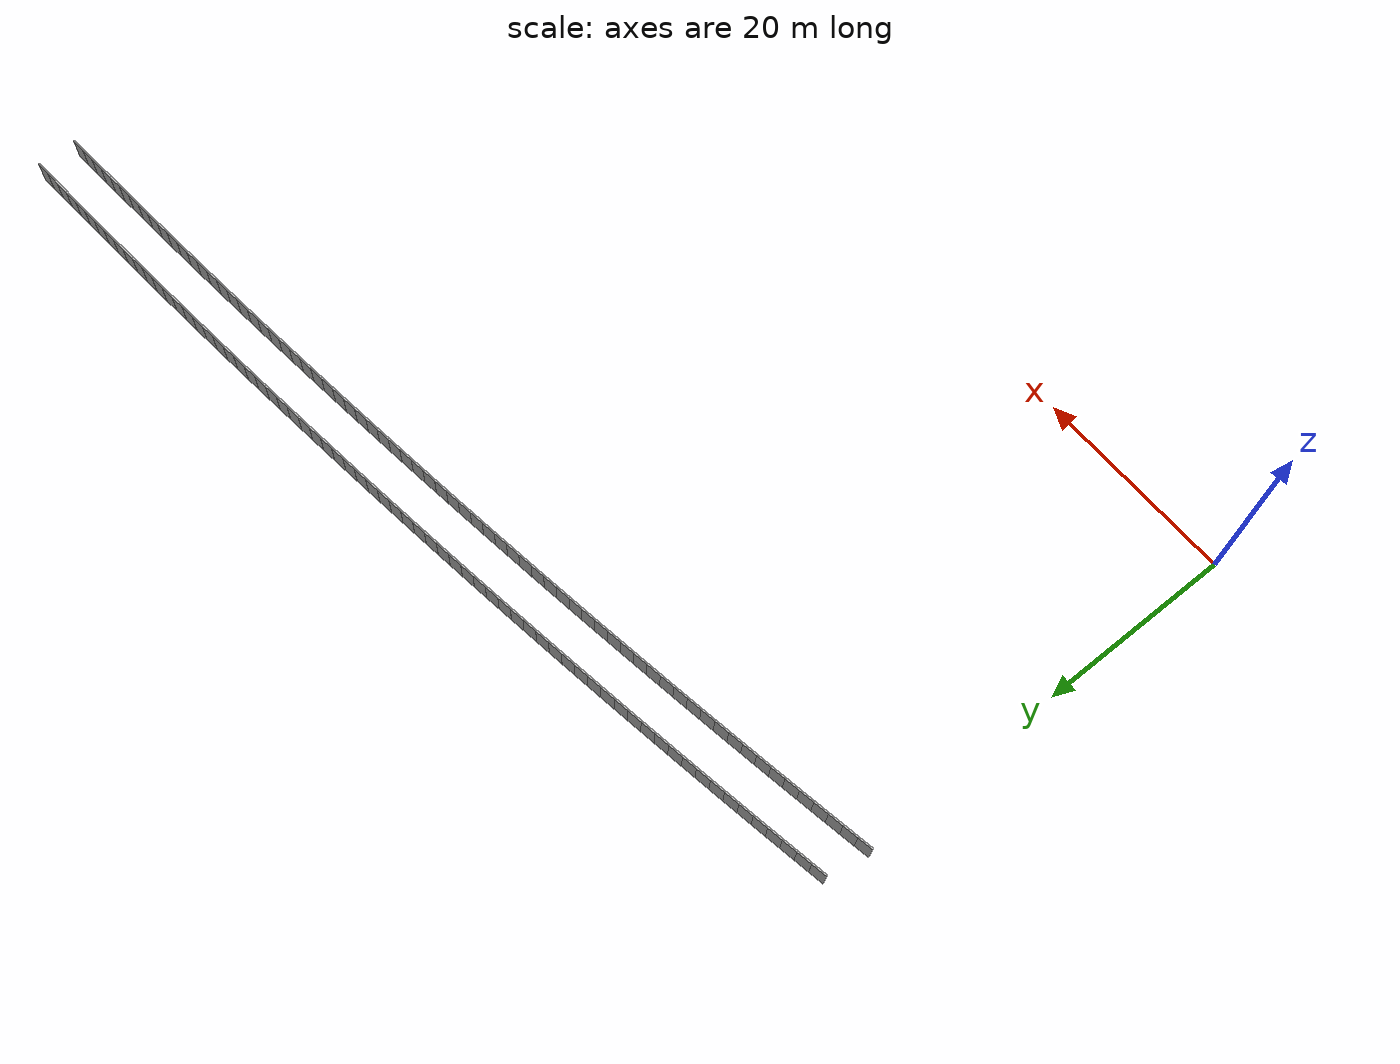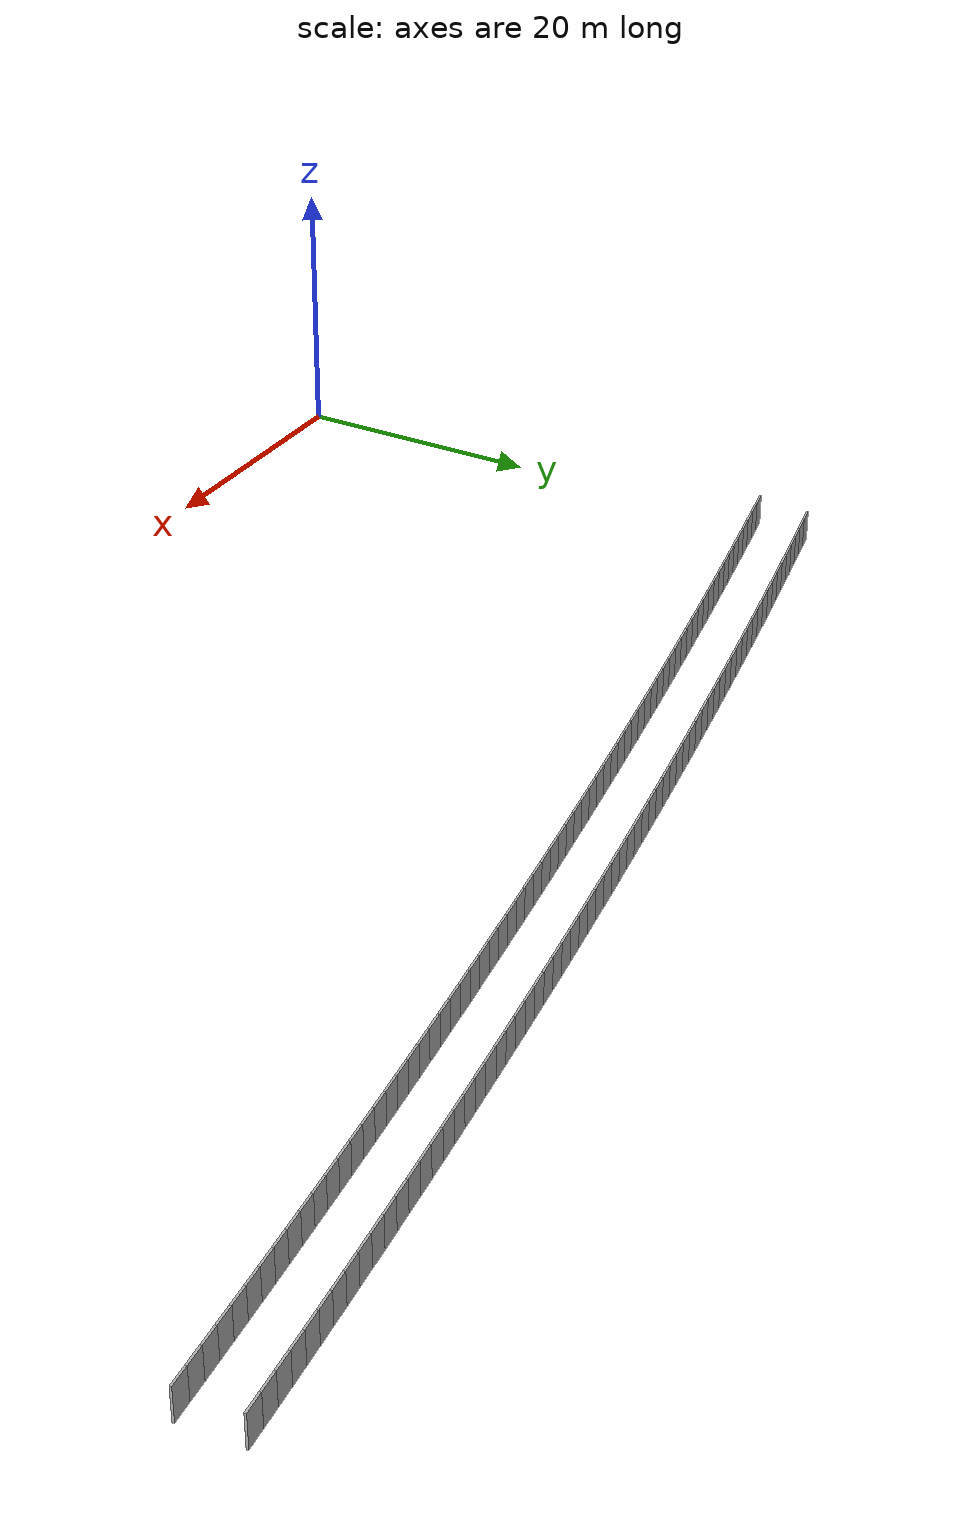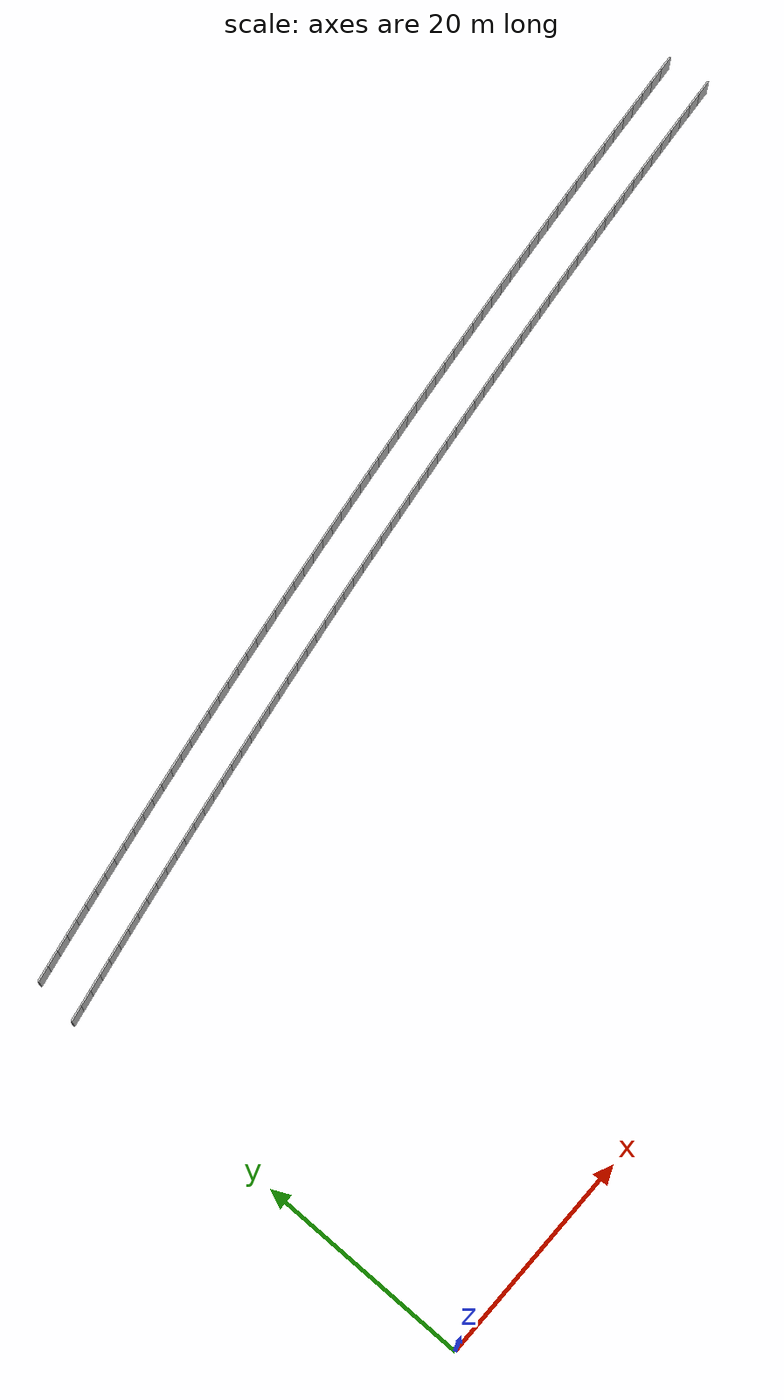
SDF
<?xml version="1.0" ?>
<sdf version="1.6">
  <model name="sps_1023">
    <pose frame="">0 0 0 0 -0 0</pose>
    <static>1</static>
    <self_collide>0</self_collide>
    <allow_auto_disable>0</allow_auto_disable>
    <link name="Wall2959">
      <kinematic>0</kinematic>
      <gravity>1</gravity>
      <self_collide>0</self_collide>
      <collision name="collision">
        <geometry>
          <box>
            <size>1.49658 0.15 2.5</size>
          </box>
        </geometry>
        <pose frame="">0 0 0 0 -0 0</pose>
      </collision>
      <visual name="visual">
        <geometry>
          <box>
            <size>1.49658 0.15 2.5</size>
          </box>
        </geometry>
        <pose frame="">0 0 0 0 -0 0</pose>
        <cast_shadows>1</cast_shadows>
        <transparency>0.0</transparency>
      </visual>
      <pose frame="">99.3093 55.6503 1.25 0 0 -3.05355</pose>
    </link>
    <link name="Wall2960">
      <kinematic>0</kinematic>
      <gravity>1</gravity>
      <self_collide>0</self_collide>
      <collision name="collision">
        <geometry>
          <box>
            <size>1.49641 0.15 2.5</size>
          </box>
        </geometry>
        <pose frame="">0 0 0 0 -0 0</pose>
      </collision>
      <visual name="visual">
        <geometry>
          <box>
            <size>1.49641 0.15 2.5</size>
          </box>
        </geometry>
        <pose frame="">0 0 0 0 -0 0</pose>
        <cast_shadows>1</cast_shadows>
        <transparency>0.0</transparency>
      </visual>
      <pose frame="">97.8187 55.5176 1.25 0 0 -3.05207</pose>
    </link>
    <link name="Wall2961">
      <kinematic>0</kinematic>
      <gravity>1</gravity>
      <self_collide>0</self_collide>
      <collision name="collision">
        <geometry>
          <box>
            <size>1.49665 0.15 2.5</size>
          </box>
        </geometry>
        <pose frame="">0 0 0 0 -0 0</pose>
      </collision>
      <visual name="visual">
        <geometry>
          <box>
            <size>1.49665 0.15 2.5</size>
          </box>
        </geometry>
        <pose frame="">0 0 0 0 -0 0</pose>
        <cast_shadows>1</cast_shadows>
        <transparency>0.0</transparency>
      </visual>
      <pose frame="">96.3282 55.3825 1.25 0 0 -3.05032</pose>
    </link>
    <link name="Wall2962">
      <kinematic>0</kinematic>
      <gravity>1</gravity>
      <self_collide>0</self_collide>
      <collision name="collision">
        <geometry>
          <box>
            <size>1.49644 0.15 2.5</size>
          </box>
        </geometry>
        <pose frame="">0 0 0 0 -0 0</pose>
      </collision>
      <visual name="visual">
        <geometry>
          <box>
            <size>1.49644 0.15 2.5</size>
          </box>
        </geometry>
        <pose frame="">0 0 0 0 -0 0</pose>
        <cast_shadows>1</cast_shadows>
        <transparency>0.0</transparency>
      </visual>
      <pose frame="">94.838 55.2449 1.25 0 0 -3.04871</pose>
    </link>
    <link name="Wall2963">
      <kinematic>0</kinematic>
      <gravity>1</gravity>
      <self_collide>0</self_collide>
      <collision name="collision">
        <geometry>
          <box>
            <size>1.49646 0.15 2.5</size>
          </box>
        </geometry>
        <pose frame="">0 0 0 0 -0 0</pose>
      </collision>
      <visual name="visual">
        <geometry>
          <box>
            <size>1.49646 0.15 2.5</size>
          </box>
        </geometry>
        <pose frame="">0 0 0 0 -0 0</pose>
        <cast_shadows>1</cast_shadows>
        <transparency>0.0</transparency>
      </visual>
      <pose frame="">93.3481 55.105 1.25 0 0 -3.04724</pose>
    </link>
    <link name="Wall2964">
      <kinematic>0</kinematic>
      <gravity>1</gravity>
      <self_collide>0</self_collide>
      <collision name="collision">
        <geometry>
          <box>
            <size>1.49647 0.15 2.5</size>
          </box>
        </geometry>
        <pose frame="">0 0 0 0 -0 0</pose>
      </collision>
      <visual name="visual">
        <geometry>
          <box>
            <size>1.49647 0.15 2.5</size>
          </box>
        </geometry>
        <pose frame="">0 0 0 0 -0 0</pose>
        <cast_shadows>1</cast_shadows>
        <transparency>0.0</transparency>
      </visual>
      <pose frame="">91.8585 54.9627 1.25 0 0 -3.04548</pose>
    </link>
    <link name="Wall2965">
      <kinematic>0</kinematic>
      <gravity>1</gravity>
      <self_collide>0</self_collide>
      <collision name="collision">
        <geometry>
          <box>
            <size>1.49656 0.15 2.5</size>
          </box>
        </geometry>
        <pose frame="">0 0 0 0 -0 0</pose>
      </collision>
      <visual name="visual">
        <geometry>
          <box>
            <size>1.49656 0.15 2.5</size>
          </box>
        </geometry>
        <pose frame="">0 0 0 0 -0 0</pose>
        <cast_shadows>1</cast_shadows>
        <transparency>0.0</transparency>
      </visual>
      <pose frame="">90.3689 54.818 1.25 0 0 -3.04401</pose>
    </link>
    <link name="Wall2966">
      <kinematic>0</kinematic>
      <gravity>1</gravity>
      <self_collide>0</self_collide>
      <collision name="collision">
        <geometry>
          <box>
            <size>1.49653 0.15 2.5</size>
          </box>
        </geometry>
        <pose frame="">0 0 0 0 -0 0</pose>
      </collision>
      <visual name="visual">
        <geometry>
          <box>
            <size>1.49653 0.15 2.5</size>
          </box>
        </geometry>
        <pose frame="">0 0 0 0 -0 0</pose>
        <cast_shadows>1</cast_shadows>
        <transparency>0.0</transparency>
      </visual>
      <pose frame="">88.8796 54.6711 1.25 0 0 -3.04257</pose>
    </link>
    <link name="Wall2967">
      <kinematic>0</kinematic>
      <gravity>1</gravity>
      <self_collide>0</self_collide>
      <collision name="collision">
        <geometry>
          <box>
            <size>1.49635 0.15 2.5</size>
          </box>
        </geometry>
        <pose frame="">0 0 0 0 -0 0</pose>
      </collision>
      <visual name="visual">
        <geometry>
          <box>
            <size>1.49635 0.15 2.5</size>
          </box>
        </geometry>
        <pose frame="">0 0 0 0 -0 0</pose>
        <cast_shadows>1</cast_shadows>
        <transparency>0.0</transparency>
      </visual>
      <pose frame="">87.3906 54.5219 1.25 0 0 -3.04088</pose>
    </link>
    <link name="Wall2968">
      <kinematic>0</kinematic>
      <gravity>1</gravity>
      <self_collide>0</self_collide>
      <collision name="collision">
        <geometry>
          <box>
            <size>1.49665 0.15 2.5</size>
          </box>
        </geometry>
        <pose frame="">0 0 0 0 -0 0</pose>
      </collision>
      <visual name="visual">
        <geometry>
          <box>
            <size>1.49665 0.15 2.5</size>
          </box>
        </geometry>
        <pose frame="">0 0 0 0 -0 0</pose>
        <cast_shadows>1</cast_shadows>
        <transparency>0.0</transparency>
      </visual>
      <pose frame="">85.9018 54.3703 1.25 0 0 -3.03934</pose>
    </link>
    <link name="Wall2969">
      <kinematic>0</kinematic>
      <gravity>1</gravity>
      <self_collide>0</self_collide>
      <collision name="collision">
        <geometry>
          <box>
            <size>1.49647 0.15 2.5</size>
          </box>
        </geometry>
        <pose frame="">0 0 0 0 -0 0</pose>
      </collision>
      <visual name="visual">
        <geometry>
          <box>
            <size>1.49647 0.15 2.5</size>
          </box>
        </geometry>
        <pose frame="">0 0 0 0 -0 0</pose>
        <cast_shadows>1</cast_shadows>
        <transparency>0.0</transparency>
      </visual>
      <pose frame="">84.4132 54.2163 1.25 0 0 -3.03769</pose>
    </link>
    <link name="Wall2970">
      <kinematic>0</kinematic>
      <gravity>1</gravity>
      <self_collide>0</self_collide>
      <collision name="collision">
        <geometry>
          <box>
            <size>1.49648 0.15 2.5</size>
          </box>
        </geometry>
        <pose frame="">0 0 0 0 -0 0</pose>
      </collision>
      <visual name="visual">
        <geometry>
          <box>
            <size>1.49648 0.15 2.5</size>
          </box>
        </geometry>
        <pose frame="">0 0 0 0 -0 0</pose>
        <cast_shadows>1</cast_shadows>
        <transparency>0.0</transparency>
      </visual>
      <pose frame="">82.9249 54.0599 1.25 0 0 -3.03609</pose>
    </link>
    <link name="Wall2971">
      <kinematic>0</kinematic>
      <gravity>1</gravity>
      <self_collide>0</self_collide>
      <collision name="collision">
        <geometry>
          <box>
            <size>1.49637 0.15 2.5</size>
          </box>
        </geometry>
        <pose frame="">0 0 0 0 -0 0</pose>
      </collision>
      <visual name="visual">
        <geometry>
          <box>
            <size>1.49637 0.15 2.5</size>
          </box>
        </geometry>
        <pose frame="">0 0 0 0 -0 0</pose>
        <cast_shadows>1</cast_shadows>
        <transparency>0.0</transparency>
      </visual>
      <pose frame="">81.437 53.9011 1.25 0 0 -3.03448</pose>
    </link>
    <link name="Wall2972">
      <kinematic>0</kinematic>
      <gravity>1</gravity>
      <self_collide>0</self_collide>
      <collision name="collision">
        <geometry>
          <box>
            <size>1.49661 0.15 2.5</size>
          </box>
        </geometry>
        <pose frame="">0 0 0 0 -0 0</pose>
      </collision>
      <visual name="visual">
        <geometry>
          <box>
            <size>1.49661 0.15 2.5</size>
          </box>
        </geometry>
        <pose frame="">0 0 0 0 -0 0</pose>
        <cast_shadows>1</cast_shadows>
        <transparency>0.0</transparency>
      </visual>
      <pose frame="">79.9492 53.74 1.25 0 0 -3.03298</pose>
    </link>
    <link name="Wall2973">
      <kinematic>0</kinematic>
      <gravity>1</gravity>
      <self_collide>0</self_collide>
      <collision name="collision">
        <geometry>
          <box>
            <size>1.49651 0.15 2.5</size>
          </box>
        </geometry>
        <pose frame="">0 0 0 0 -0 0</pose>
      </collision>
      <visual name="visual">
        <geometry>
          <box>
            <size>1.49651 0.15 2.5</size>
          </box>
        </geometry>
        <pose frame="">0 0 0 0 -0 0</pose>
        <cast_shadows>1</cast_shadows>
        <transparency>0.0</transparency>
      </visual>
      <pose frame="">78.4616 53.5766 1.25 0 0 -3.03137</pose>
    </link>
    <link name="Wall2974">
      <kinematic>0</kinematic>
      <gravity>1</gravity>
      <self_collide>0</self_collide>
      <collision name="collision">
        <geometry>
          <box>
            <size>1.49635 0.15 2.5</size>
          </box>
        </geometry>
        <pose frame="">0 0 0 0 -0 0</pose>
      </collision>
      <visual name="visual">
        <geometry>
          <box>
            <size>1.49635 0.15 2.5</size>
          </box>
        </geometry>
        <pose frame="">0 0 0 0 -0 0</pose>
        <cast_shadows>1</cast_shadows>
        <transparency>0.0</transparency>
      </visual>
      <pose frame="">76.9744 53.4108 1.25 0 0 -3.02976</pose>
    </link>
    <link name="Wall2975">
      <kinematic>0</kinematic>
      <gravity>1</gravity>
      <self_collide>0</self_collide>
      <collision name="collision">
        <geometry>
          <box>
            <size>1.49664 0.15 2.5</size>
          </box>
        </geometry>
        <pose frame="">0 0 0 0 -0 0</pose>
      </collision>
      <visual name="visual">
        <geometry>
          <box>
            <size>1.49664 0.15 2.5</size>
          </box>
        </geometry>
        <pose frame="">0 0 0 0 -0 0</pose>
        <cast_shadows>1</cast_shadows>
        <transparency>0.0</transparency>
      </visual>
      <pose frame="">75.4874 53.2425 1.25 0 0 -3.02802</pose>
    </link>
    <link name="Wall2976">
      <kinematic>0</kinematic>
      <gravity>1</gravity>
      <self_collide>0</self_collide>
      <collision name="collision">
        <geometry>
          <box>
            <size>1.49644 0.15 2.5</size>
          </box>
        </geometry>
        <pose frame="">0 0 0 0 -0 0</pose>
      </collision>
      <visual name="visual">
        <geometry>
          <box>
            <size>1.49644 0.15 2.5</size>
          </box>
        </geometry>
        <pose frame="">0 0 0 0 -0 0</pose>
        <cast_shadows>1</cast_shadows>
        <transparency>0.0</transparency>
      </visual>
      <pose frame="">74.0006 53.0719 1.25 0 0 -3.02669</pose>
    </link>
    <link name="Wall2977">
      <kinematic>0</kinematic>
      <gravity>1</gravity>
      <self_collide>0</self_collide>
      <collision name="collision">
        <geometry>
          <box>
            <size>1.49662 0.15 2.5</size>
          </box>
        </geometry>
        <pose frame="">0 0 0 0 -0 0</pose>
      </collision>
      <visual name="visual">
        <geometry>
          <box>
            <size>1.49662 0.15 2.5</size>
          </box>
        </geometry>
        <pose frame="">0 0 0 0 -0 0</pose>
        <cast_shadows>1</cast_shadows>
        <transparency>0.0</transparency>
      </visual>
      <pose frame="">72.5141 52.899 1.25 0 0 -3.02494</pose>
    </link>
    <link name="Wall2978">
      <kinematic>0</kinematic>
      <gravity>1</gravity>
      <self_collide>0</self_collide>
      <collision name="collision">
        <geometry>
          <box>
            <size>1.49639 0.15 2.5</size>
          </box>
        </geometry>
        <pose frame="">0 0 0 0 -0 0</pose>
      </collision>
      <visual name="visual">
        <geometry>
          <box>
            <size>1.49639 0.15 2.5</size>
          </box>
        </geometry>
        <pose frame="">0 0 0 0 -0 0</pose>
        <cast_shadows>1</cast_shadows>
        <transparency>0.0</transparency>
      </visual>
      <pose frame="">71.0279 52.7237 1.25 0 0 -3.02344</pose>
    </link>
    <link name="Wall2979">
      <kinematic>0</kinematic>
      <gravity>1</gravity>
      <self_collide>0</self_collide>
      <collision name="collision">
        <geometry>
          <box>
            <size>1.49656 0.15 2.5</size>
          </box>
        </geometry>
        <pose frame="">0 0 0 0 -0 0</pose>
      </collision>
      <visual name="visual">
        <geometry>
          <box>
            <size>1.49656 0.15 2.5</size>
          </box>
        </geometry>
        <pose frame="">0 0 0 0 -0 0</pose>
        <cast_shadows>1</cast_shadows>
        <transparency>0.0</transparency>
      </visual>
      <pose frame="">69.542 52.5461 1.25 0 0 -3.02181</pose>
    </link>
    <link name="Wall2980">
      <kinematic>0</kinematic>
      <gravity>1</gravity>
      <self_collide>0</self_collide>
      <collision name="collision">
        <geometry>
          <box>
            <size>1.49658 0.15 2.5</size>
          </box>
        </geometry>
        <pose frame="">0 0 0 0 -0 0</pose>
      </collision>
      <visual name="visual">
        <geometry>
          <box>
            <size>1.49658 0.15 2.5</size>
          </box>
        </geometry>
        <pose frame="">0 0 0 0 -0 0</pose>
        <cast_shadows>1</cast_shadows>
        <transparency>0.0</transparency>
      </visual>
      <pose frame="">68.0562 52.3662 1.25 0 0 -3.02037</pose>
    </link>
    <link name="Wall2981">
      <kinematic>0</kinematic>
      <gravity>1</gravity>
      <self_collide>0</self_collide>
      <collision name="collision">
        <geometry>
          <box>
            <size>1.49647 0.15 2.5</size>
          </box>
        </geometry>
        <pose frame="">0 0 0 0 -0 0</pose>
      </collision>
      <visual name="visual">
        <geometry>
          <box>
            <size>1.49647 0.15 2.5</size>
          </box>
        </geometry>
        <pose frame="">0 0 0 0 -0 0</pose>
        <cast_shadows>1</cast_shadows>
        <transparency>0.0</transparency>
      </visual>
      <pose frame="">66.5709 52.1839 1.25 0 0 -3.0186</pose>
    </link>
    <link name="Wall2982">
      <kinematic>0</kinematic>
      <gravity>1</gravity>
      <self_collide>0</self_collide>
      <collision name="collision">
        <geometry>
          <box>
            <size>1.49636 0.15 2.5</size>
          </box>
        </geometry>
        <pose frame="">0 0 0 0 -0 0</pose>
      </collision>
      <visual name="visual">
        <geometry>
          <box>
            <size>1.49636 0.15 2.5</size>
          </box>
        </geometry>
        <pose frame="">0 0 0 0 -0 0</pose>
        <cast_shadows>1</cast_shadows>
        <transparency>0.0</transparency>
      </visual>
      <pose frame="">65.0859 51.9993 1.25 0 0 -3.01723</pose>
    </link>
    <link name="Wall2983">
      <kinematic>0</kinematic>
      <gravity>1</gravity>
      <self_collide>0</self_collide>
      <collision name="collision">
        <geometry>
          <box>
            <size>1.4965 0.15 2.5</size>
          </box>
        </geometry>
        <pose frame="">0 0 0 0 -0 0</pose>
      </collision>
      <visual name="visual">
        <geometry>
          <box>
            <size>1.4965 0.15 2.5</size>
          </box>
        </geometry>
        <pose frame="">0 0 0 0 -0 0</pose>
        <cast_shadows>1</cast_shadows>
        <transparency>0.0</transparency>
      </visual>
      <pose frame="">63.6012 51.8124 1.25 0 0 -3.01548</pose>
    </link>
    <link name="Wall2984">
      <kinematic>0</kinematic>
      <gravity>1</gravity>
      <self_collide>0</self_collide>
      <collision name="collision">
        <geometry>
          <box>
            <size>1.49659 0.15 2.5</size>
          </box>
        </geometry>
        <pose frame="">0 0 0 0 -0 0</pose>
      </collision>
      <visual name="visual">
        <geometry>
          <box>
            <size>1.49659 0.15 2.5</size>
          </box>
        </geometry>
        <pose frame="">0 0 0 0 -0 0</pose>
        <cast_shadows>1</cast_shadows>
        <transparency>0.0</transparency>
      </visual>
      <pose frame="">62.1167 51.6229 1.25 0 0 -3.01376</pose>
    </link>
    <link name="Wall2985">
      <kinematic>0</kinematic>
      <gravity>1</gravity>
      <self_collide>0</self_collide>
      <collision name="collision">
        <geometry>
          <box>
            <size>1.49648 0.15 2.5</size>
          </box>
        </geometry>
        <pose frame="">0 0 0 0 -0 0</pose>
      </collision>
      <visual name="visual">
        <geometry>
          <box>
            <size>1.49648 0.15 2.5</size>
          </box>
        </geometry>
        <pose frame="">0 0 0 0 -0 0</pose>
        <cast_shadows>1</cast_shadows>
        <transparency>0.0</transparency>
      </visual>
      <pose frame="">60.6325 51.4311 1.25 0 0 -3.01239</pose>
    </link>
    <link name="Wall2986">
      <kinematic>0</kinematic>
      <gravity>1</gravity>
      <self_collide>0</self_collide>
      <collision name="collision">
        <geometry>
          <box>
            <size>1.49661 0.15 2.5</size>
          </box>
        </geometry>
        <pose frame="">0 0 0 0 -0 0</pose>
      </collision>
      <visual name="visual">
        <geometry>
          <box>
            <size>1.49661 0.15 2.5</size>
          </box>
        </geometry>
        <pose frame="">0 0 0 0 -0 0</pose>
        <cast_shadows>1</cast_shadows>
        <transparency>0.0</transparency>
      </visual>
      <pose frame="">59.1486 51.2371 1.25 0 0 -3.0108</pose>
    </link>
    <link name="Wall2987">
      <kinematic>0</kinematic>
      <gravity>1</gravity>
      <self_collide>0</self_collide>
      <collision name="collision">
        <geometry>
          <box>
            <size>1.4965 0.15 2.5</size>
          </box>
        </geometry>
        <pose frame="">0 0 0 0 -0 0</pose>
      </collision>
      <visual name="visual">
        <geometry>
          <box>
            <size>1.4965 0.15 2.5</size>
          </box>
        </geometry>
        <pose frame="">0 0 0 0 -0 0</pose>
        <cast_shadows>1</cast_shadows>
        <transparency>0.0</transparency>
      </visual>
      <pose frame="">57.6649 51.0407 1.25 0 0 -3.00918</pose>
    </link>
    <link name="Wall2988">
      <kinematic>0</kinematic>
      <gravity>1</gravity>
      <self_collide>0</self_collide>
      <collision name="collision">
        <geometry>
          <box>
            <size>1.4964 0.15 2.5</size>
          </box>
        </geometry>
        <pose frame="">0 0 0 0 -0 0</pose>
      </collision>
      <visual name="visual">
        <geometry>
          <box>
            <size>1.4964 0.15 2.5</size>
          </box>
        </geometry>
        <pose frame="">0 0 0 0 -0 0</pose>
        <cast_shadows>1</cast_shadows>
        <transparency>0.0</transparency>
      </visual>
      <pose frame="">56.1818 50.8419 1.25 0 0 -3.00753</pose>
    </link>
    <link name="Wall2989">
      <kinematic>0</kinematic>
      <gravity>1</gravity>
      <self_collide>0</self_collide>
      <collision name="collision">
        <geometry>
          <box>
            <size>1.49651 0.15 2.5</size>
          </box>
        </geometry>
        <pose frame="">0 0 0 0 -0 0</pose>
      </collision>
      <visual name="visual">
        <geometry>
          <box>
            <size>1.49651 0.15 2.5</size>
          </box>
        </geometry>
        <pose frame="">0 0 0 0 -0 0</pose>
        <cast_shadows>1</cast_shadows>
        <transparency>0.0</transparency>
      </visual>
      <pose frame="">54.6989 50.6408 1.25 0 0 -3.00606</pose>
    </link>
    <link name="Wall2990">
      <kinematic>0</kinematic>
      <gravity>1</gravity>
      <self_collide>0</self_collide>
      <collision name="collision">
        <geometry>
          <box>
            <size>1.49647 0.15 2.5</size>
          </box>
        </geometry>
        <pose frame="">0 0 0 0 -0 0</pose>
      </collision>
      <visual name="visual">
        <geometry>
          <box>
            <size>1.49647 0.15 2.5</size>
          </box>
        </geometry>
        <pose frame="">0 0 0 0 -0 0</pose>
        <cast_shadows>1</cast_shadows>
        <transparency>0.0</transparency>
      </visual>
      <pose frame="">53.2163 50.4374 1.25 0 0 -3.00445</pose>
    </link>
    <link name="Wall2991">
      <kinematic>0</kinematic>
      <gravity>1</gravity>
      <self_collide>0</self_collide>
      <collision name="collision">
        <geometry>
          <box>
            <size>1.49657 0.15 2.5</size>
          </box>
        </geometry>
        <pose frame="">0 0 0 0 -0 0</pose>
      </collision>
      <visual name="visual">
        <geometry>
          <box>
            <size>1.49657 0.15 2.5</size>
          </box>
        </geometry>
        <pose frame="">0 0 0 0 -0 0</pose>
        <cast_shadows>1</cast_shadows>
        <transparency>0.0</transparency>
      </visual>
      <pose frame="">51.734 50.2316 1.25 0 0 -3.00281</pose>
    </link>
    <link name="Wall2992">
      <kinematic>0</kinematic>
      <gravity>1</gravity>
      <self_collide>0</self_collide>
      <collision name="collision">
        <geometry>
          <box>
            <size>1.49653 0.15 2.5</size>
          </box>
        </geometry>
        <pose frame="">0 0 0 0 -0 0</pose>
      </collision>
      <visual name="visual">
        <geometry>
          <box>
            <size>1.49653 0.15 2.5</size>
          </box>
        </geometry>
        <pose frame="">0 0 0 0 -0 0</pose>
        <cast_shadows>1</cast_shadows>
        <transparency>0.0</transparency>
      </visual>
      <pose frame="">50.252 50.0234 1.25 0 0 -3.00124</pose>
    </link>
    <link name="Wall2993">
      <kinematic>0</kinematic>
      <gravity>1</gravity>
      <self_collide>0</self_collide>
      <collision name="collision">
        <geometry>
          <box>
            <size>1.49646 0.15 2.5</size>
          </box>
        </geometry>
        <pose frame="">0 0 0 0 -0 0</pose>
      </collision>
      <visual name="visual">
        <geometry>
          <box>
            <size>1.49646 0.15 2.5</size>
          </box>
        </geometry>
        <pose frame="">0 0 0 0 -0 0</pose>
        <cast_shadows>1</cast_shadows>
        <transparency>0.0</transparency>
      </visual>
      <pose frame="">48.7704 49.8128 1.25 0 0 -2.99955</pose>
    </link>
    <link name="Wall2994">
      <kinematic>0</kinematic>
      <gravity>1</gravity>
      <self_collide>0</self_collide>
      <collision name="collision">
        <geometry>
          <box>
            <size>1.4964 0.15 2.5</size>
          </box>
        </geometry>
        <pose frame="">0 0 0 0 -0 0</pose>
      </collision>
      <visual name="visual">
        <geometry>
          <box>
            <size>1.4964 0.15 2.5</size>
          </box>
        </geometry>
        <pose frame="">0 0 0 0 -0 0</pose>
        <cast_shadows>1</cast_shadows>
        <transparency>0.0</transparency>
      </visual>
      <pose frame="">47.2892 49.5999 1.25 0 0 -2.9981</pose>
    </link>
    <link name="Wall2995">
      <kinematic>0</kinematic>
      <gravity>1</gravity>
      <self_collide>0</self_collide>
      <collision name="collision">
        <geometry>
          <box>
            <size>1.49656 0.15 2.5</size>
          </box>
        </geometry>
        <pose frame="">0 0 0 0 -0 0</pose>
      </collision>
      <visual name="visual">
        <geometry>
          <box>
            <size>1.49656 0.15 2.5</size>
          </box>
        </geometry>
        <pose frame="">0 0 0 0 -0 0</pose>
        <cast_shadows>1</cast_shadows>
        <transparency>0.0</transparency>
      </visual>
      <pose frame="">45.8082 49.3847 1.25 0 0 -2.99651</pose>
    </link>
    <link name="Wall2996">
      <kinematic>0</kinematic>
      <gravity>1</gravity>
      <self_collide>0</self_collide>
      <collision name="collision">
        <geometry>
          <box>
            <size>1.4964 0.15 2.5</size>
          </box>
        </geometry>
        <pose frame="">0 0 0 0 -0 0</pose>
      </collision>
      <visual name="visual">
        <geometry>
          <box>
            <size>1.4964 0.15 2.5</size>
          </box>
        </geometry>
        <pose frame="">0 0 0 0 -0 0</pose>
        <cast_shadows>1</cast_shadows>
        <transparency>0.0</transparency>
      </visual>
      <pose frame="">44.3277 49.1672 1.25 0 0 -2.99497</pose>
    </link>
    <link name="Wall2997">
      <kinematic>0</kinematic>
      <gravity>1</gravity>
      <self_collide>0</self_collide>
      <collision name="collision">
        <geometry>
          <box>
            <size>1.49666 0.15 2.5</size>
          </box>
        </geometry>
        <pose frame="">0 0 0 0 -0 0</pose>
      </collision>
      <visual name="visual">
        <geometry>
          <box>
            <size>1.49666 0.15 2.5</size>
          </box>
        </geometry>
        <pose frame="">0 0 0 0 -0 0</pose>
        <cast_shadows>1</cast_shadows>
        <transparency>0.0</transparency>
      </visual>
      <pose frame="">42.8474 48.9473 1.25 0 0 -2.99326</pose>
    </link>
    <link name="Wall2998">
      <kinematic>0</kinematic>
      <gravity>1</gravity>
      <self_collide>0</self_collide>
      <collision name="collision">
        <geometry>
          <box>
            <size>1.49636 0.15 2.5</size>
          </box>
        </geometry>
        <pose frame="">0 0 0 0 -0 0</pose>
      </collision>
      <visual name="visual">
        <geometry>
          <box>
            <size>1.49636 0.15 2.5</size>
          </box>
        </geometry>
        <pose frame="">0 0 0 0 -0 0</pose>
        <cast_shadows>1</cast_shadows>
        <transparency>0.0</transparency>
      </visual>
      <pose frame="">41.3675 48.7251 1.25 0 0 -2.99187</pose>
    </link>
    <link name="Wall2999">
      <kinematic>0</kinematic>
      <gravity>1</gravity>
      <self_collide>0</self_collide>
      <collision name="collision">
        <geometry>
          <box>
            <size>1.4965 0.15 2.5</size>
          </box>
        </geometry>
        <pose frame="">0 0 0 0 -0 0</pose>
      </collision>
      <visual name="visual">
        <geometry>
          <box>
            <size>1.4965 0.15 2.5</size>
          </box>
        </geometry>
        <pose frame="">0 0 0 0 -0 0</pose>
        <cast_shadows>1</cast_shadows>
        <transparency>0.0</transparency>
      </visual>
      <pose frame="">39.888 48.5006 1.25 0 0 -2.99015</pose>
    </link>
    <link name="Wall3000">
      <kinematic>0</kinematic>
      <gravity>1</gravity>
      <self_collide>0</self_collide>
      <collision name="collision">
        <geometry>
          <box>
            <size>1.49648 0.15 2.5</size>
          </box>
        </geometry>
        <pose frame="">0 0 0 0 -0 0</pose>
      </collision>
      <visual name="visual">
        <geometry>
          <box>
            <size>1.49648 0.15 2.5</size>
          </box>
        </geometry>
        <pose frame="">0 0 0 0 -0 0</pose>
        <cast_shadows>1</cast_shadows>
        <transparency>0.0</transparency>
      </visual>
      <pose frame="">38.4088 48.2737 1.25 0 0 -2.98862</pose>
    </link>
    <link name="Wall3001">
      <kinematic>0</kinematic>
      <gravity>1</gravity>
      <self_collide>0</self_collide>
      <collision name="collision">
        <geometry>
          <box>
            <size>1.49648 0.15 2.5</size>
          </box>
        </geometry>
        <pose frame="">0 0 0 0 -0 0</pose>
      </collision>
      <visual name="visual">
        <geometry>
          <box>
            <size>1.49648 0.15 2.5</size>
          </box>
        </geometry>
        <pose frame="">0 0 0 0 -0 0</pose>
        <cast_shadows>1</cast_shadows>
        <transparency>0.0</transparency>
      </visual>
      <pose frame="">36.93 48.0445 1.25 0 0 -2.98701</pose>
    </link>
    <link name="Wall3002">
      <kinematic>0</kinematic>
      <gravity>1</gravity>
      <self_collide>0</self_collide>
      <collision name="collision">
        <geometry>
          <box>
            <size>1.49661 0.15 2.5</size>
          </box>
        </geometry>
        <pose frame="">0 0 0 0 -0 0</pose>
      </collision>
      <visual name="visual">
        <geometry>
          <box>
            <size>1.49661 0.15 2.5</size>
          </box>
        </geometry>
        <pose frame="">0 0 0 0 -0 0</pose>
        <cast_shadows>1</cast_shadows>
        <transparency>0.0</transparency>
      </visual>
      <pose frame="">35.4514 47.8129 1.25 0 0 -2.98541</pose>
    </link>
    <link name="Wall3003">
      <kinematic>0</kinematic>
      <gravity>1</gravity>
      <self_collide>0</self_collide>
      <collision name="collision">
        <geometry>
          <box>
            <size>1.49638 0.15 2.5</size>
          </box>
        </geometry>
        <pose frame="">0 0 0 0 -0 0</pose>
      </collision>
      <visual name="visual">
        <geometry>
          <box>
            <size>1.49638 0.15 2.5</size>
          </box>
        </geometry>
        <pose frame="">0 0 0 0 -0 0</pose>
        <cast_shadows>1</cast_shadows>
        <transparency>0.0</transparency>
      </visual>
      <pose frame="">33.9733 47.5789 1.25 0 0 -2.98378</pose>
    </link>
    <link name="Wall3004">
      <kinematic>0</kinematic>
      <gravity>1</gravity>
      <self_collide>0</self_collide>
      <collision name="collision">
        <geometry>
          <box>
            <size>1.49658 0.15 2.5</size>
          </box>
        </geometry>
        <pose frame="">0 0 0 0 -0 0</pose>
      </collision>
      <visual name="visual">
        <geometry>
          <box>
            <size>1.49658 0.15 2.5</size>
          </box>
        </geometry>
        <pose frame="">0 0 0 0 -0 0</pose>
        <cast_shadows>1</cast_shadows>
        <transparency>0.0</transparency>
      </visual>
      <pose frame="">32.4957 47.3425 1.25 0 0 -2.98215</pose>
    </link>
    <link name="Wall3005">
      <kinematic>0</kinematic>
      <gravity>1</gravity>
      <self_collide>0</self_collide>
      <collision name="collision">
        <geometry>
          <box>
            <size>1.49648 0.15 2.5</size>
          </box>
        </geometry>
        <pose frame="">0 0 0 0 -0 0</pose>
      </collision>
      <visual name="visual">
        <geometry>
          <box>
            <size>1.49648 0.15 2.5</size>
          </box>
        </geometry>
        <pose frame="">0 0 0 0 -0 0</pose>
        <cast_shadows>1</cast_shadows>
        <transparency>0.0</transparency>
      </visual>
      <pose frame="">31.0183 47.1039 1.25 0 0 -2.98078</pose>
    </link>
    <link name="Wall3006">
      <kinematic>0</kinematic>
      <gravity>1</gravity>
      <self_collide>0</self_collide>
      <collision name="collision">
        <geometry>
          <box>
            <size>1.49653 0.15 2.5</size>
          </box>
        </geometry>
        <pose frame="">0 0 0 0 -0 0</pose>
      </collision>
      <visual name="visual">
        <geometry>
          <box>
            <size>1.49653 0.15 2.5</size>
          </box>
        </geometry>
        <pose frame="">0 0 0 0 -0 0</pose>
        <cast_shadows>1</cast_shadows>
        <transparency>0.0</transparency>
      </visual>
      <pose frame="">29.5413 46.863 1.25 0 0 -2.97905</pose>
    </link>
    <link name="Wall3007">
      <kinematic>0</kinematic>
      <gravity>1</gravity>
      <self_collide>0</self_collide>
      <collision name="collision">
        <geometry>
          <box>
            <size>1.49657 0.15 2.5</size>
          </box>
        </geometry>
        <pose frame="">0 0 0 0 -0 0</pose>
      </collision>
      <visual name="visual">
        <geometry>
          <box>
            <size>1.49657 0.15 2.5</size>
          </box>
        </geometry>
        <pose frame="">0 0 0 0 -0 0</pose>
        <cast_shadows>1</cast_shadows>
        <transparency>0.0</transparency>
      </visual>
      <pose frame="">28.0647 46.6196 1.25 0 0 -2.9774</pose>
    </link>
    <link name="Wall3008">
      <kinematic>0</kinematic>
      <gravity>1</gravity>
      <self_collide>0</self_collide>
      <collision name="collision">
        <geometry>
          <box>
            <size>1.49644 0.15 2.5</size>
          </box>
        </geometry>
        <pose frame="">0 0 0 0 -0 0</pose>
      </collision>
      <visual name="visual">
        <geometry>
          <box>
            <size>1.49644 0.15 2.5</size>
          </box>
        </geometry>
        <pose frame="">0 0 0 0 -0 0</pose>
        <cast_shadows>1</cast_shadows>
        <transparency>0.0</transparency>
      </visual>
      <pose frame="">26.5885 46.3739 1.25 0 0 -2.97593</pose>
    </link>
    <link name="Wall3009">
      <kinematic>0</kinematic>
      <gravity>1</gravity>
      <self_collide>0</self_collide>
      <collision name="collision">
        <geometry>
          <box>
            <size>1.49654 0.15 2.5</size>
          </box>
        </geometry>
        <pose frame="">0 0 0 0 -0 0</pose>
      </collision>
      <visual name="visual">
        <geometry>
          <box>
            <size>1.49654 0.15 2.5</size>
          </box>
        </geometry>
        <pose frame="">0 0 0 0 -0 0</pose>
        <cast_shadows>1</cast_shadows>
        <transparency>0.0</transparency>
      </visual>
      <pose frame="">25.1127 46.1259 1.25 0 0 -2.97429</pose>
    </link>
    <link name="Wall3010">
      <kinematic>0</kinematic>
      <gravity>1</gravity>
      <self_collide>0</self_collide>
      <collision name="collision">
        <geometry>
          <box>
            <size>1.49646 0.15 2.5</size>
          </box>
        </geometry>
        <pose frame="">0 0 0 0 -0 0</pose>
      </collision>
      <visual name="visual">
        <geometry>
          <box>
            <size>1.49646 0.15 2.5</size>
          </box>
        </geometry>
        <pose frame="">0 0 0 0 -0 0</pose>
        <cast_shadows>1</cast_shadows>
        <transparency>0.0</transparency>
      </visual>
      <pose frame="">23.6373 45.8755 1.25 0 0 -2.97267</pose>
    </link>
    <link name="Wall3011">
      <kinematic>0</kinematic>
      <gravity>1</gravity>
      <self_collide>0</self_collide>
      <collision name="collision">
        <geometry>
          <box>
            <size>1.49654 0.15 2.5</size>
          </box>
        </geometry>
        <pose frame="">0 0 0 0 -0 0</pose>
      </collision>
      <visual name="visual">
        <geometry>
          <box>
            <size>1.49654 0.15 2.5</size>
          </box>
        </geometry>
        <pose frame="">0 0 0 0 -0 0</pose>
        <cast_shadows>1</cast_shadows>
        <transparency>0.0</transparency>
      </visual>
      <pose frame="">22.1623 45.6228 1.25 0 0 -2.97115</pose>
    </link>
    <link name="Wall3012">
      <kinematic>0</kinematic>
      <gravity>1</gravity>
      <self_collide>0</self_collide>
      <collision name="collision">
        <geometry>
          <box>
            <size>1.49627 0.15 2.5</size>
          </box>
        </geometry>
        <pose frame="">0 0 0 0 -0 0</pose>
      </collision>
      <visual name="visual">
        <geometry>
          <box>
            <size>1.49627 0.15 2.5</size>
          </box>
        </geometry>
        <pose frame="">0 0 0 0 -0 0</pose>
        <cast_shadows>1</cast_shadows>
        <transparency>0.0</transparency>
      </visual>
      <pose frame="">20.6877 45.3678 1.25 0 0 -2.96954</pose>
    </link>
    <link name="Wall3013">
      <kinematic>0</kinematic>
      <gravity>1</gravity>
      <self_collide>0</self_collide>
      <collision name="collision">
        <geometry>
          <box>
            <size>1.49644 0.15 2.5</size>
          </box>
        </geometry>
        <pose frame="">0 0 0 0 -0 0</pose>
      </collision>
      <visual name="visual">
        <geometry>
          <box>
            <size>1.49644 0.15 2.5</size>
          </box>
        </geometry>
        <pose frame="">0 0 0 0 -0 0</pose>
        <cast_shadows>1</cast_shadows>
        <transparency>0.0</transparency>
      </visual>
      <pose frame="">19.2136 45.1106 1.25 0 0 -2.9682</pose>
    </link>
    <link name="Wall3014">
      <kinematic>0</kinematic>
      <gravity>1</gravity>
      <self_collide>0</self_collide>
      <collision name="collision">
        <geometry>
          <box>
            <size>1.49647 0.15 2.5</size>
          </box>
        </geometry>
        <pose frame="">0 0 0 0 -0 0</pose>
      </collision>
      <visual name="visual">
        <geometry>
          <box>
            <size>1.49647 0.15 2.5</size>
          </box>
        </geometry>
        <pose frame="">0 0 0 0 -0 0</pose>
        <cast_shadows>1</cast_shadows>
        <transparency>0.0</transparency>
      </visual>
      <pose frame="">17.7399 44.8511 1.25 0 0 -2.96642</pose>
    </link>
    <link name="Wall3015">
      <kinematic>0</kinematic>
      <gravity>1</gravity>
      <self_collide>0</self_collide>
      <collision name="collision">
        <geometry>
          <box>
            <size>1.49654 0.15 2.5</size>
          </box>
        </geometry>
        <pose frame="">0 0 0 0 -0 0</pose>
      </collision>
      <visual name="visual">
        <geometry>
          <box>
            <size>1.49654 0.15 2.5</size>
          </box>
        </geometry>
        <pose frame="">0 0 0 0 -0 0</pose>
        <cast_shadows>1</cast_shadows>
        <transparency>0.0</transparency>
      </visual>
      <pose frame="">16.2665 44.5891 1.25 0 0 -2.96477</pose>
    </link>
    <link name="Wall3016">
      <kinematic>0</kinematic>
      <gravity>1</gravity>
      <self_collide>0</self_collide>
      <collision name="collision">
        <geometry>
          <box>
            <size>1.49659 0.15 2.5</size>
          </box>
        </geometry>
        <pose frame="">0 0 0 0 -0 0</pose>
      </collision>
      <visual name="visual">
        <geometry>
          <box>
            <size>1.49659 0.15 2.5</size>
          </box>
        </geometry>
        <pose frame="">0 0 0 0 -0 0</pose>
        <cast_shadows>1</cast_shadows>
        <transparency>0.0</transparency>
      </visual>
      <pose frame="">14.7934 44.3247 1.25 0 0 -2.9632</pose>
    </link>
    <link name="Wall3017">
      <kinematic>0</kinematic>
      <gravity>1</gravity>
      <self_collide>0</self_collide>
      <collision name="collision">
        <geometry>
          <box>
            <size>1.49651 0.15 2.5</size>
          </box>
        </geometry>
        <pose frame="">0 0 0 0 -0 0</pose>
      </collision>
      <visual name="visual">
        <geometry>
          <box>
            <size>1.49651 0.15 2.5</size>
          </box>
        </geometry>
        <pose frame="">0 0 0 0 -0 0</pose>
        <cast_shadows>1</cast_shadows>
        <transparency>0.0</transparency>
      </visual>
      <pose frame="">13.3209 44.058 1.25 0 0 -2.96166</pose>
    </link>
    <link name="Wall3018">
      <kinematic>0</kinematic>
      <gravity>1</gravity>
      <self_collide>0</self_collide>
      <collision name="collision">
        <geometry>
          <box>
            <size>1.49637 0.15 2.5</size>
          </box>
        </geometry>
        <pose frame="">0 0 0 0 -0 0</pose>
      </collision>
      <visual name="visual">
        <geometry>
          <box>
            <size>1.49637 0.15 2.5</size>
          </box>
        </geometry>
        <pose frame="">0 0 0 0 -0 0</pose>
        <cast_shadows>1</cast_shadows>
        <transparency>0.0</transparency>
      </visual>
      <pose frame="">11.8488 43.7891 1.25 0 0 -2.96015</pose>
    </link>
    <link name="Wall3019">
      <kinematic>0</kinematic>
      <gravity>1</gravity>
      <self_collide>0</self_collide>
      <collision name="collision">
        <geometry>
          <box>
            <size>1.49665 0.15 2.5</size>
          </box>
        </geometry>
        <pose frame="">0 0 0 0 -0 0</pose>
      </collision>
      <visual name="visual">
        <geometry>
          <box>
            <size>1.49665 0.15 2.5</size>
          </box>
        </geometry>
        <pose frame="">0 0 0 0 -0 0</pose>
        <cast_shadows>1</cast_shadows>
        <transparency>0.0</transparency>
      </visual>
      <pose frame="">10.3771 43.5178 1.25 0 0 -2.95844</pose>
    </link>
    <link name="Wall3020">
      <kinematic>0</kinematic>
      <gravity>1</gravity>
      <self_collide>0</self_collide>
      <collision name="collision">
        <geometry>
          <box>
            <size>1.49649 0.15 2.5</size>
          </box>
        </geometry>
        <pose frame="">0 0 0 0 -0 0</pose>
      </collision>
      <visual name="visual">
        <geometry>
          <box>
            <size>1.49649 0.15 2.5</size>
          </box>
        </geometry>
        <pose frame="">0 0 0 0 -0 0</pose>
        <cast_shadows>1</cast_shadows>
        <transparency>0.0</transparency>
      </visual>
      <pose frame="">8.90575 43.244 1.25 0 0 -2.9568</pose>
    </link>
    <link name="Wall3021">
      <kinematic>0</kinematic>
      <gravity>1</gravity>
      <self_collide>0</self_collide>
      <collision name="collision">
        <geometry>
          <box>
            <size>1.49666 0.15 2.5</size>
          </box>
        </geometry>
        <pose frame="">0 0 0 0 -0 0</pose>
      </collision>
      <visual name="visual">
        <geometry>
          <box>
            <size>1.49666 0.15 2.5</size>
          </box>
        </geometry>
        <pose frame="">0 0 0 0 -0 0</pose>
        <cast_shadows>1</cast_shadows>
        <transparency>0.0</transparency>
      </visual>
      <pose frame="">7.43487 42.9679 1.25 0 0 -2.95529</pose>
    </link>
    <link name="Wall3022">
      <kinematic>0</kinematic>
      <gravity>1</gravity>
      <self_collide>0</self_collide>
      <collision name="collision">
        <geometry>
          <box>
            <size>1.49635 0.15 2.5</size>
          </box>
        </geometry>
        <pose frame="">0 0 0 0 -0 0</pose>
      </collision>
      <visual name="visual">
        <geometry>
          <box>
            <size>1.49635 0.15 2.5</size>
          </box>
        </geometry>
        <pose frame="">0 0 0 0 -0 0</pose>
        <cast_shadows>1</cast_shadows>
        <transparency>0.0</transparency>
      </visual>
      <pose frame="">5.96447 42.6896 1.25 0 0 -2.95376</pose>
    </link>
    <link name="Wall3023">
      <kinematic>0</kinematic>
      <gravity>1</gravity>
      <self_collide>0</self_collide>
      <collision name="collision">
        <geometry>
          <box>
            <size>1.49659 0.15 2.5</size>
          </box>
        </geometry>
        <pose frame="">0 0 0 0 -0 0</pose>
      </collision>
      <visual name="visual">
        <geometry>
          <box>
            <size>1.49659 0.15 2.5</size>
          </box>
        </geometry>
        <pose frame="">0 0 0 0 -0 0</pose>
        <cast_shadows>1</cast_shadows>
        <transparency>0.0</transparency>
      </visual>
      <pose frame="">4.49456 42.4089 1.25 0 0 -2.95204</pose>
    </link>
    <link name="Wall3024">
      <kinematic>0</kinematic>
      <gravity>1</gravity>
      <self_collide>0</self_collide>
      <collision name="collision">
        <geometry>
          <box>
            <size>1.49647 0.15 2.5</size>
          </box>
        </geometry>
        <pose frame="">0 0 0 0 -0 0</pose>
      </collision>
      <visual name="visual">
        <geometry>
          <box>
            <size>1.49647 0.15 2.5</size>
          </box>
        </geometry>
        <pose frame="">0 0 0 0 -0 0</pose>
        <cast_shadows>1</cast_shadows>
        <transparency>0.0</transparency>
      </visual>
      <pose frame="">3.02505 42.1258 1.25 0 0 -2.95053</pose>
    </link>
    <link name="Wall3025">
      <kinematic>0</kinematic>
      <gravity>1</gravity>
      <self_collide>0</self_collide>
      <collision name="collision">
        <geometry>
          <box>
            <size>1.49642 0.15 2.5</size>
          </box>
        </geometry>
        <pose frame="">0 0 0 0 -0 0</pose>
      </collision>
      <visual name="visual">
        <geometry>
          <box>
            <size>1.49642 0.15 2.5</size>
          </box>
        </geometry>
        <pose frame="">0 0 0 0 -0 0</pose>
        <cast_shadows>1</cast_shadows>
        <transparency>0.0</transparency>
      </visual>
      <pose frame="">1.55605 41.8405 1.25 0 0 -2.94899</pose>
    </link>
    <link name="Wall3026">
      <kinematic>0</kinematic>
      <gravity>1</gravity>
      <self_collide>0</self_collide>
      <collision name="collision">
        <geometry>
          <box>
            <size>1.49657 0.15 2.5</size>
          </box>
        </geometry>
        <pose frame="">0 0 0 0 -0 0</pose>
      </collision>
      <visual name="visual">
        <geometry>
          <box>
            <size>1.49657 0.15 2.5</size>
          </box>
        </geometry>
        <pose frame="">0 0 0 0 -0 0</pose>
        <cast_shadows>1</cast_shadows>
        <transparency>0.0</transparency>
      </visual>
      <pose frame="">0.0874551 41.5529 1.25 0 0 -2.94743</pose>
    </link>
    <link name="Wall5570">
      <kinematic>0</kinematic>
      <gravity>1</gravity>
      <self_collide>0</self_collide>
      <collision name="collision">
        <geometry>
          <box>
            <size>1.50308 0.15 2.5</size>
          </box>
        </geometry>
        <pose frame="">0 0 0 0 -0 0</pose>
      </collision>
      <visual name="visual">
        <geometry>
          <box>
            <size>1.50308 0.15 2.5</size>
          </box>
        </geometry>
        <pose frame="">0 0 0 0 -0 0</pose>
        <cast_shadows>1</cast_shadows>
        <transparency>0.0</transparency>
      </visual>
      <pose frame="">98.9415 59.7736 1.25 0 0 -3.05352</pose>
    </link>
    <link name="Wall5571">
      <kinematic>0</kinematic>
      <gravity>1</gravity>
      <self_collide>0</self_collide>
      <collision name="collision">
        <geometry>
          <box>
            <size>1.50323 0.15 2.5</size>
          </box>
        </geometry>
        <pose frame="">0 0 0 0 -0 0</pose>
      </collision>
      <visual name="visual">
        <geometry>
          <box>
            <size>1.50323 0.15 2.5</size>
          </box>
        </geometry>
        <pose frame="">0 0 0 0 -0 0</pose>
        <cast_shadows>1</cast_shadows>
        <transparency>0.0</transparency>
      </visual>
      <pose frame="">97.4442 59.6402 1.25 0 0 -3.05194</pose>
    </link>
    <link name="Wall5572">
      <kinematic>0</kinematic>
      <gravity>1</gravity>
      <self_collide>0</self_collide>
      <collision name="collision">
        <geometry>
          <box>
            <size>1.50302 0.15 2.5</size>
          </box>
        </geometry>
        <pose frame="">0 0 0 0 -0 0</pose>
      </collision>
      <visual name="visual">
        <geometry>
          <box>
            <size>1.50302 0.15 2.5</size>
          </box>
        </geometry>
        <pose frame="">0 0 0 0 -0 0</pose>
        <cast_shadows>1</cast_shadows>
        <transparency>0.0</transparency>
      </visual>
      <pose frame="">95.9473 59.5044 1.25 0 0 -3.0503</pose>
    </link>
    <link name="Wall5573">
      <kinematic>0</kinematic>
      <gravity>1</gravity>
      <self_collide>0</self_collide>
      <collision name="collision">
        <geometry>
          <box>
            <size>1.50312 0.15 2.5</size>
          </box>
        </geometry>
        <pose frame="">0 0 0 0 -0 0</pose>
      </collision>
      <visual name="visual">
        <geometry>
          <box>
            <size>1.50312 0.15 2.5</size>
          </box>
        </geometry>
        <pose frame="">0 0 0 0 -0 0</pose>
        <cast_shadows>1</cast_shadows>
        <transparency>0.0</transparency>
      </visual>
      <pose frame="">94.4506 59.3662 1.25 0 0 -3.04876</pose>
    </link>
    <link name="Wall5574">
      <kinematic>0</kinematic>
      <gravity>1</gravity>
      <self_collide>0</self_collide>
      <collision name="collision">
        <geometry>
          <box>
            <size>1.50308 0.15 2.5</size>
          </box>
        </geometry>
        <pose frame="">0 0 0 0 -0 0</pose>
      </collision>
      <visual name="visual">
        <geometry>
          <box>
            <size>1.50308 0.15 2.5</size>
          </box>
        </geometry>
        <pose frame="">0 0 0 0 -0 0</pose>
        <cast_shadows>1</cast_shadows>
        <transparency>0.0</transparency>
      </visual>
      <pose frame="">92.954 59.2257 1.25 0 0 -3.04725</pose>
    </link>
    <link name="Wall5575">
      <kinematic>0</kinematic>
      <gravity>1</gravity>
      <self_collide>0</self_collide>
      <collision name="collision">
        <geometry>
          <box>
            <size>1.50289 0.15 2.5</size>
          </box>
        </geometry>
        <pose frame="">0 0 0 0 -0 0</pose>
      </collision>
      <visual name="visual">
        <geometry>
          <box>
            <size>1.50289 0.15 2.5</size>
          </box>
        </geometry>
        <pose frame="">0 0 0 0 -0 0</pose>
        <cast_shadows>1</cast_shadows>
        <transparency>0.0</transparency>
      </visual>
      <pose frame="">91.4578 59.0829 1.25 0 0 -3.0456</pose>
    </link>
    <link name="Wall5576">
      <kinematic>0</kinematic>
      <gravity>1</gravity>
      <self_collide>0</self_collide>
      <collision name="collision">
        <geometry>
          <box>
            <size>1.5032 0.15 2.5</size>
          </box>
        </geometry>
        <pose frame="">0 0 0 0 -0 0</pose>
      </collision>
      <visual name="visual">
        <geometry>
          <box>
            <size>1.5032 0.15 2.5</size>
          </box>
        </geometry>
        <pose frame="">0 0 0 0 -0 0</pose>
        <cast_shadows>1</cast_shadows>
        <transparency>0.0</transparency>
      </visual>
      <pose frame="">89.9618 58.9376 1.25 0 0 -3.04391</pose>
    </link>
    <link name="Wall5577">
      <kinematic>0</kinematic>
      <gravity>1</gravity>
      <self_collide>0</self_collide>
      <collision name="collision">
        <geometry>
          <box>
            <size>1.50315 0.15 2.5</size>
          </box>
        </geometry>
        <pose frame="">0 0 0 0 -0 0</pose>
      </collision>
      <visual name="visual">
        <geometry>
          <box>
            <size>1.50315 0.15 2.5</size>
          </box>
        </geometry>
        <pose frame="">0 0 0 0 -0 0</pose>
        <cast_shadows>1</cast_shadows>
        <transparency>0.0</transparency>
      </visual>
      <pose frame="">88.4659 58.79 1.25 0 0 -3.0426</pose>
    </link>
    <link name="Wall5578">
      <kinematic>0</kinematic>
      <gravity>1</gravity>
      <self_collide>0</self_collide>
      <collision name="collision">
        <geometry>
          <box>
            <size>1.50323 0.15 2.5</size>
          </box>
        </geometry>
        <pose frame="">0 0 0 0 -0 0</pose>
      </collision>
      <visual name="visual">
        <geometry>
          <box>
            <size>1.50323 0.15 2.5</size>
          </box>
        </geometry>
        <pose frame="">0 0 0 0 -0 0</pose>
        <cast_shadows>1</cast_shadows>
        <transparency>0.0</transparency>
      </visual>
      <pose frame="">86.9702 58.6401 1.25 0 0 -3.04081</pose>
    </link>
    <link name="Wall5579">
      <kinematic>0</kinematic>
      <gravity>1</gravity>
      <self_collide>0</self_collide>
      <collision name="collision">
        <geometry>
          <box>
            <size>1.50284 0.15 2.5</size>
          </box>
        </geometry>
        <pose frame="">0 0 0 0 -0 0</pose>
      </collision>
      <visual name="visual">
        <geometry>
          <box>
            <size>1.50284 0.15 2.5</size>
          </box>
        </geometry>
        <pose frame="">0 0 0 0 -0 0</pose>
        <cast_shadows>1</cast_shadows>
        <transparency>0.0</transparency>
      </visual>
      <pose frame="">85.4749 58.4878 1.25 0 0 -3.03935</pose>
    </link>
    <link name="Wall5580">
      <kinematic>0</kinematic>
      <gravity>1</gravity>
      <self_collide>0</self_collide>
      <collision name="collision">
        <geometry>
          <box>
            <size>1.50311 0.15 2.5</size>
          </box>
        </geometry>
        <pose frame="">0 0 0 0 -0 0</pose>
      </collision>
      <visual name="visual">
        <geometry>
          <box>
            <size>1.50311 0.15 2.5</size>
          </box>
        </geometry>
        <pose frame="">0 0 0 0 -0 0</pose>
        <cast_shadows>1</cast_shadows>
        <transparency>0.0</transparency>
      </visual>
      <pose frame="">83.9799 58.3331 1.25 0 0 -3.03762</pose>
    </link>
    <link name="Wall5581">
      <kinematic>0</kinematic>
      <gravity>1</gravity>
      <self_collide>0</self_collide>
      <collision name="collision">
        <geometry>
          <box>
            <size>1.50318 0.15 2.5</size>
          </box>
        </geometry>
        <pose frame="">0 0 0 0 -0 0</pose>
      </collision>
      <visual name="visual">
        <geometry>
          <box>
            <size>1.50318 0.15 2.5</size>
          </box>
        </geometry>
        <pose frame="">0 0 0 0 -0 0</pose>
        <cast_shadows>1</cast_shadows>
        <transparency>0.0</transparency>
      </visual>
      <pose frame="">82.485 58.1759 1.25 0 0 -3.03603</pose>
    </link>
    <link name="Wall5582">
      <kinematic>0</kinematic>
      <gravity>1</gravity>
      <self_collide>0</self_collide>
      <collision name="collision">
        <geometry>
          <box>
            <size>1.50299 0.15 2.5</size>
          </box>
        </geometry>
        <pose frame="">0 0 0 0 -0 0</pose>
      </collision>
      <visual name="visual">
        <geometry>
          <box>
            <size>1.50299 0.15 2.5</size>
          </box>
        </geometry>
        <pose frame="">0 0 0 0 -0 0</pose>
        <cast_shadows>1</cast_shadows>
        <transparency>0.0</transparency>
      </visual>
      <pose frame="">80.9904 58.0164 1.25 0 0 -3.03455</pose>
    </link>
    <link name="Wall5583">
      <kinematic>0</kinematic>
      <gravity>1</gravity>
      <self_collide>0</self_collide>
      <collision name="collision">
        <geometry>
          <box>
            <size>1.50307 0.15 2.5</size>
          </box>
        </geometry>
        <pose frame="">0 0 0 0 -0 0</pose>
      </collision>
      <visual name="visual">
        <geometry>
          <box>
            <size>1.50307 0.15 2.5</size>
          </box>
        </geometry>
        <pose frame="">0 0 0 0 -0 0</pose>
        <cast_shadows>1</cast_shadows>
        <transparency>0.0</transparency>
      </visual>
      <pose frame="">79.4961 57.8546 1.25 0 0 -3.03292</pose>
    </link>
    <link name="Wall5584">
      <kinematic>0</kinematic>
      <gravity>1</gravity>
      <self_collide>0</self_collide>
      <collision name="collision">
        <geometry>
          <box>
            <size>1.50315 0.15 2.5</size>
          </box>
        </geometry>
        <pose frame="">0 0 0 0 -0 0</pose>
      </collision>
      <visual name="visual">
        <geometry>
          <box>
            <size>1.50315 0.15 2.5</size>
          </box>
        </geometry>
        <pose frame="">0 0 0 0 -0 0</pose>
        <cast_shadows>1</cast_shadows>
        <transparency>0.0</transparency>
      </visual>
      <pose frame="">78.002 57.6904 1.25 0 0 -3.03133</pose>
    </link>
    <link name="Wall5585">
      <kinematic>0</kinematic>
      <gravity>1</gravity>
      <self_collide>0</self_collide>
      <collision name="collision">
        <geometry>
          <box>
            <size>1.50297 0.15 2.5</size>
          </box>
        </geometry>
        <pose frame="">0 0 0 0 -0 0</pose>
      </collision>
      <visual name="visual">
        <geometry>
          <box>
            <size>1.50297 0.15 2.5</size>
          </box>
        </geometry>
        <pose frame="">0 0 0 0 -0 0</pose>
        <cast_shadows>1</cast_shadows>
        <transparency>0.0</transparency>
      </visual>
      <pose frame="">76.5082 57.5239 1.25 0 0 -3.02985</pose>
    </link>
    <link name="Wall5586">
      <kinematic>0</kinematic>
      <gravity>1</gravity>
      <self_collide>0</self_collide>
      <collision name="collision">
        <geometry>
          <box>
            <size>1.50325 0.15 2.5</size>
          </box>
        </geometry>
        <pose frame="">0 0 0 0 -0 0</pose>
      </collision>
      <visual name="visual">
        <geometry>
          <box>
            <size>1.50325 0.15 2.5</size>
          </box>
        </geometry>
        <pose frame="">0 0 0 0 -0 0</pose>
        <cast_shadows>1</cast_shadows>
        <transparency>0.0</transparency>
      </visual>
      <pose frame="">75.0146 57.355 1.25 0 0 -3.02815</pose>
    </link>
    <link name="Wall5587">
      <kinematic>0</kinematic>
      <gravity>1</gravity>
      <self_collide>0</self_collide>
      <collision name="collision">
        <geometry>
          <box>
            <size>1.5029 0.15 2.5</size>
          </box>
        </geometry>
        <pose frame="">0 0 0 0 -0 0</pose>
      </collision>
      <visual name="visual">
        <geometry>
          <box>
            <size>1.5029 0.15 2.5</size>
          </box>
        </geometry>
        <pose frame="">0 0 0 0 -0 0</pose>
        <cast_shadows>1</cast_shadows>
        <transparency>0.0</transparency>
      </visual>
      <pose frame="">73.5214 57.1837 1.25 0 0 -3.02661</pose>
    </link>
    <link name="Wall5588">
      <kinematic>0</kinematic>
      <gravity>1</gravity>
      <self_collide>0</self_collide>
      <collision name="collision">
        <geometry>
          <box>
            <size>1.50318 0.15 2.5</size>
          </box>
        </geometry>
        <pose frame="">0 0 0 0 -0 0</pose>
      </collision>
      <visual name="visual">
        <geometry>
          <box>
            <size>1.50318 0.15 2.5</size>
          </box>
        </geometry>
        <pose frame="">0 0 0 0 -0 0</pose>
        <cast_shadows>1</cast_shadows>
        <transparency>0.0</transparency>
      </visual>
      <pose frame="">72.0284 57.0101 1.25 0 0 -3.02504</pose>
    </link>
    <link name="Wall5589">
      <kinematic>0</kinematic>
      <gravity>1</gravity>
      <self_collide>0</self_collide>
      <collision name="collision">
        <geometry>
          <box>
            <size>1.50309 0.15 2.5</size>
          </box>
        </geometry>
        <pose frame="">0 0 0 0 -0 0</pose>
      </collision>
      <visual name="visual">
        <geometry>
          <box>
            <size>1.50309 0.15 2.5</size>
          </box>
        </geometry>
        <pose frame="">0 0 0 0 -0 0</pose>
        <cast_shadows>1</cast_shadows>
        <transparency>0.0</transparency>
      </visual>
      <pose frame="">70.5356 56.8341 1.25 0 0 -3.02344</pose>
    </link>
    <link name="Wall5590">
      <kinematic>0</kinematic>
      <gravity>1</gravity>
      <self_collide>0</self_collide>
      <collision name="collision">
        <geometry>
          <box>
            <size>1.5032 0.15 2.5</size>
          </box>
        </geometry>
        <pose frame="">0 0 0 0 -0 0</pose>
      </collision>
      <visual name="visual">
        <geometry>
          <box>
            <size>1.5032 0.15 2.5</size>
          </box>
        </geometry>
        <pose frame="">0 0 0 0 -0 0</pose>
        <cast_shadows>1</cast_shadows>
        <transparency>0.0</transparency>
      </visual>
      <pose frame="">69.0431 56.6557 1.25 0 0 -3.02181</pose>
    </link>
    <link name="Wall5591">
      <kinematic>0</kinematic>
      <gravity>1</gravity>
      <self_collide>0</self_collide>
      <collision name="collision">
        <geometry>
          <box>
            <size>1.50306 0.15 2.5</size>
          </box>
        </geometry>
        <pose frame="">0 0 0 0 -0 0</pose>
      </collision>
      <visual name="visual">
        <geometry>
          <box>
            <size>1.50306 0.15 2.5</size>
          </box>
        </geometry>
        <pose frame="">0 0 0 0 -0 0</pose>
        <cast_shadows>1</cast_shadows>
        <transparency>0.0</transparency>
      </visual>
      <pose frame="">67.5508 56.4749 1.25 0 0 -3.0202</pose>
    </link>
    <link name="Wall5592">
      <kinematic>0</kinematic>
      <gravity>1</gravity>
      <self_collide>0</self_collide>
      <collision name="collision">
        <geometry>
          <box>
            <size>1.50293 0.15 2.5</size>
          </box>
        </geometry>
        <pose frame="">0 0 0 0 -0 0</pose>
      </collision>
      <visual name="visual">
        <geometry>
          <box>
            <size>1.50293 0.15 2.5</size>
          </box>
        </geometry>
        <pose frame="">0 0 0 0 -0 0</pose>
        <cast_shadows>1</cast_shadows>
        <transparency>0.0</transparency>
      </visual>
      <pose frame="">66.059 56.2917 1.25 0 0 -3.0186</pose>
    </link>
    <link name="Wall5593">
      <kinematic>0</kinematic>
      <gravity>1</gravity>
      <self_collide>0</self_collide>
      <collision name="collision">
        <geometry>
          <box>
            <size>1.503 0.15 2.5</size>
          </box>
        </geometry>
        <pose frame="">0 0 0 0 -0 0</pose>
      </collision>
      <visual name="visual">
        <geometry>
          <box>
            <size>1.503 0.15 2.5</size>
          </box>
        </geometry>
        <pose frame="">0 0 0 0 -0 0</pose>
        <cast_shadows>1</cast_shadows>
        <transparency>0.0</transparency>
      </visual>
      <pose frame="">64.5676 56.1063 1.25 0 0 -3.01725</pose>
    </link>
    <link name="Wall5594">
      <kinematic>0</kinematic>
      <gravity>1</gravity>
      <self_collide>0</self_collide>
      <collision name="collision">
        <geometry>
          <box>
            <size>1.50314 0.15 2.5</size>
          </box>
        </geometry>
        <pose frame="">0 0 0 0 -0 0</pose>
      </collision>
      <visual name="visual">
        <geometry>
          <box>
            <size>1.50314 0.15 2.5</size>
          </box>
        </geometry>
        <pose frame="">0 0 0 0 -0 0</pose>
        <cast_shadows>1</cast_shadows>
        <transparency>0.0</transparency>
      </visual>
      <pose frame="">63.0763 55.9186 1.25 0 0 -3.01555</pose>
    </link>
    <link name="Wall5595">
      <kinematic>0</kinematic>
      <gravity>1</gravity>
      <self_collide>0</self_collide>
      <collision name="collision">
        <geometry>
          <box>
            <size>1.50302 0.15 2.5</size>
          </box>
        </geometry>
        <pose frame="">0 0 0 0 -0 0</pose>
      </collision>
      <visual name="visual">
        <geometry>
          <box>
            <size>1.50302 0.15 2.5</size>
          </box>
        </geometry>
        <pose frame="">0 0 0 0 -0 0</pose>
        <cast_shadows>1</cast_shadows>
        <transparency>0.0</transparency>
      </visual>
      <pose frame="">61.5853 55.7284 1.25 0 0 -3.0139</pose>
    </link>
    <link name="Wall5596">
      <kinematic>0</kinematic>
      <gravity>1</gravity>
      <self_collide>0</self_collide>
      <collision name="collision">
        <geometry>
          <box>
            <size>1.50296 0.15 2.5</size>
          </box>
        </geometry>
        <pose frame="">0 0 0 0 -0 0</pose>
      </collision>
      <visual name="visual">
        <geometry>
          <box>
            <size>1.50296 0.15 2.5</size>
          </box>
        </geometry>
        <pose frame="">0 0 0 0 -0 0</pose>
        <cast_shadows>1</cast_shadows>
        <transparency>0.0</transparency>
      </visual>
      <pose frame="">60.0947 55.5358 1.25 0 0 -3.0123</pose>
    </link>
    <link name="Wall5597">
      <kinematic>0</kinematic>
      <gravity>1</gravity>
      <self_collide>0</self_collide>
      <collision name="collision">
        <geometry>
          <box>
            <size>1.50328 0.15 2.5</size>
          </box>
        </geometry>
        <pose frame="">0 0 0 0 -0 0</pose>
      </collision>
      <visual name="visual">
        <geometry>
          <box>
            <size>1.50328 0.15 2.5</size>
          </box>
        </geometry>
        <pose frame="">0 0 0 0 -0 0</pose>
        <cast_shadows>1</cast_shadows>
        <transparency>0.0</transparency>
      </visual>
      <pose frame="">58.6042 55.3408 1.25 0 0 -3.01069</pose>
    </link>
    <link name="Wall5598">
      <kinematic>0</kinematic>
      <gravity>1</gravity>
      <self_collide>0</self_collide>
      <collision name="collision">
        <geometry>
          <box>
            <size>1.50317 0.15 2.5</size>
          </box>
        </geometry>
        <pose frame="">0 0 0 0 -0 0</pose>
      </collision>
      <visual name="visual">
        <geometry>
          <box>
            <size>1.50317 0.15 2.5</size>
          </box>
        </geometry>
        <pose frame="">0 0 0 0 -0 0</pose>
        <cast_shadows>1</cast_shadows>
        <transparency>0.0</transparency>
      </visual>
      <pose frame="">57.114 55.1434 1.25 0 0 -3.00908</pose>
    </link>
    <link name="Wall5599">
      <kinematic>0</kinematic>
      <gravity>1</gravity>
      <self_collide>0</self_collide>
      <collision name="collision">
        <geometry>
          <box>
            <size>1.50304 0.15 2.5</size>
          </box>
        </geometry>
        <pose frame="">0 0 0 0 -0 0</pose>
      </collision>
      <visual name="visual">
        <geometry>
          <box>
            <size>1.50304 0.15 2.5</size>
          </box>
        </geometry>
        <pose frame="">0 0 0 0 -0 0</pose>
        <cast_shadows>1</cast_shadows>
        <transparency>0.0</transparency>
      </visual>
      <pose frame="">55.6243 54.9437 1.25 0 0 -3.00759</pose>
    </link>
    <link name="Wall5600">
      <kinematic>0</kinematic>
      <gravity>1</gravity>
      <self_collide>0</self_collide>
      <collision name="collision">
        <geometry>
          <box>
            <size>1.50299 0.15 2.5</size>
          </box>
        </geometry>
        <pose frame="">0 0 0 0 -0 0</pose>
      </collision>
      <visual name="visual">
        <geometry>
          <box>
            <size>1.50299 0.15 2.5</size>
          </box>
        </geometry>
        <pose frame="">0 0 0 0 -0 0</pose>
        <cast_shadows>1</cast_shadows>
        <transparency>0.0</transparency>
      </visual>
      <pose frame="">54.1349 54.7417 1.25 0 0 -3.00599</pose>
    </link>
    <link name="Wall5601">
      <kinematic>0</kinematic>
      <gravity>1</gravity>
      <self_collide>0</self_collide>
      <collision name="collision">
        <geometry>
          <box>
            <size>1.50311 0.15 2.5</size>
          </box>
        </geometry>
        <pose frame="">0 0 0 0 -0 0</pose>
      </collision>
      <visual name="visual">
        <geometry>
          <box>
            <size>1.50311 0.15 2.5</size>
          </box>
        </geometry>
        <pose frame="">0 0 0 0 -0 0</pose>
        <cast_shadows>1</cast_shadows>
        <transparency>0.0</transparency>
      </visual>
      <pose frame="">52.6458 54.5374 1.25 0 0 -3.00453</pose>
    </link>
    <link name="Wall5602">
      <kinematic>0</kinematic>
      <gravity>1</gravity>
      <self_collide>0</self_collide>
      <collision name="collision">
        <geometry>
          <box>
            <size>1.50329 0.15 2.5</size>
          </box>
        </geometry>
        <pose frame="">0 0 0 0 -0 0</pose>
      </collision>
      <visual name="visual">
        <geometry>
          <box>
            <size>1.50329 0.15 2.5</size>
          </box>
        </geometry>
        <pose frame="">0 0 0 0 -0 0</pose>
        <cast_shadows>1</cast_shadows>
        <transparency>0.0</transparency>
      </visual>
      <pose frame="">51.1569 54.3307 1.25 0 0 -3.00278</pose>
    </link>
    <link name="Wall5603">
      <kinematic>0</kinematic>
      <gravity>1</gravity>
      <self_collide>0</self_collide>
      <collision name="collision">
        <geometry>
          <box>
            <size>1.50293 0.15 2.5</size>
          </box>
        </geometry>
        <pose frame="">0 0 0 0 -0 0</pose>
      </collision>
      <visual name="visual">
        <geometry>
          <box>
            <size>1.50293 0.15 2.5</size>
          </box>
        </geometry>
        <pose frame="">0 0 0 0 -0 0</pose>
        <cast_shadows>1</cast_shadows>
        <transparency>0.0</transparency>
      </visual>
      <pose frame="">49.6684 54.1216 1.25 0 0 -3.00127</pose>
    </link>
    <link name="Wall5604">
      <kinematic>0</kinematic>
      <gravity>1</gravity>
      <self_collide>0</self_collide>
      <collision name="collision">
        <geometry>
          <box>
            <size>1.50315 0.15 2.5</size>
          </box>
        </geometry>
        <pose frame="">0 0 0 0 -0 0</pose>
      </collision>
      <visual name="visual">
        <geometry>
          <box>
            <size>1.50315 0.15 2.5</size>
          </box>
        </geometry>
        <pose frame="">0 0 0 0 -0 0</pose>
        <cast_shadows>1</cast_shadows>
        <transparency>0.0</transparency>
      </visual>
      <pose frame="">48.1803 53.9102 1.25 0 0 -2.99969</pose>
    </link>
    <link name="Wall5605">
      <kinematic>0</kinematic>
      <gravity>1</gravity>
      <self_collide>0</self_collide>
      <collision name="collision">
        <geometry>
          <box>
            <size>1.50307 0.15 2.5</size>
          </box>
        </geometry>
        <pose frame="">0 0 0 0 -0 0</pose>
      </collision>
      <visual name="visual">
        <geometry>
          <box>
            <size>1.50307 0.15 2.5</size>
          </box>
        </geometry>
        <pose frame="">0 0 0 0 -0 0</pose>
        <cast_shadows>1</cast_shadows>
        <transparency>0.0</transparency>
      </visual>
      <pose frame="">46.6924 53.6964 1.25 0 0 -2.99804</pose>
    </link>
    <link name="Wall5606">
      <kinematic>0</kinematic>
      <gravity>1</gravity>
      <self_collide>0</self_collide>
      <collision name="collision">
        <geometry>
          <box>
            <size>1.50299 0.15 2.5</size>
          </box>
        </geometry>
        <pose frame="">0 0 0 0 -0 0</pose>
      </collision>
      <visual name="visual">
        <geometry>
          <box>
            <size>1.50299 0.15 2.5</size>
          </box>
        </geometry>
        <pose frame="">0 0 0 0 -0 0</pose>
        <cast_shadows>1</cast_shadows>
        <transparency>0.0</transparency>
      </visual>
      <pose frame="">45.205 53.4802 1.25 0 0 -2.99643</pose>
    </link>
    <link name="Wall5607">
      <kinematic>0</kinematic>
      <gravity>1</gravity>
      <self_collide>0</self_collide>
      <collision name="collision">
        <geometry>
          <box>
            <size>1.50313 0.15 2.5</size>
          </box>
        </geometry>
        <pose frame="">0 0 0 0 -0 0</pose>
      </collision>
      <visual name="visual">
        <geometry>
          <box>
            <size>1.50313 0.15 2.5</size>
          </box>
        </geometry>
        <pose frame="">0 0 0 0 -0 0</pose>
        <cast_shadows>1</cast_shadows>
        <transparency>0.0</transparency>
      </visual>
      <pose frame="">43.7179 53.2617 1.25 0 0 -2.99497</pose>
    </link>
    <link name="Wall5608">
      <kinematic>0</kinematic>
      <gravity>1</gravity>
      <self_collide>0</self_collide>
      <collision name="collision">
        <geometry>
          <box>
            <size>1.50303 0.15 2.5</size>
          </box>
        </geometry>
        <pose frame="">0 0 0 0 -0 0</pose>
      </collision>
      <visual name="visual">
        <geometry>
          <box>
            <size>1.50303 0.15 2.5</size>
          </box>
        </geometry>
        <pose frame="">0 0 0 0 -0 0</pose>
        <cast_shadows>1</cast_shadows>
        <transparency>0.0</transparency>
      </visual>
      <pose frame="">42.2312 53.041 1.25 0 0 -2.99348</pose>
    </link>
    <link name="Wall5609">
      <kinematic>0</kinematic>
      <gravity>1</gravity>
      <self_collide>0</self_collide>
      <collision name="collision">
        <geometry>
          <box>
            <size>1.50305 0.15 2.5</size>
          </box>
        </geometry>
        <pose frame="">0 0 0 0 -0 0</pose>
      </collision>
      <visual name="visual">
        <geometry>
          <box>
            <size>1.50305 0.15 2.5</size>
          </box>
        </geometry>
        <pose frame="">0 0 0 0 -0 0</pose>
        <cast_shadows>1</cast_shadows>
        <transparency>0.0</transparency>
      </visual>
      <pose frame="">40.7448 52.8179 1.25 0 0 -2.99176</pose>
    </link>
    <link name="Wall5610">
      <kinematic>0</kinematic>
      <gravity>1</gravity>
      <self_collide>0</self_collide>
      <collision name="collision">
        <geometry>
          <box>
            <size>1.50305 0.15 2.5</size>
          </box>
        </geometry>
        <pose frame="">0 0 0 0 -0 0</pose>
      </collision>
      <visual name="visual">
        <geometry>
          <box>
            <size>1.50305 0.15 2.5</size>
          </box>
        </geometry>
        <pose frame="">0 0 0 0 -0 0</pose>
        <cast_shadows>1</cast_shadows>
        <transparency>0.0</transparency>
      </visual>
      <pose frame="">39.2588 52.5923 1.25 0 0 -2.99012</pose>
    </link>
    <link name="Wall5611">
      <kinematic>0</kinematic>
      <gravity>1</gravity>
      <self_collide>0</self_collide>
      <collision name="collision">
        <geometry>
          <box>
            <size>1.50317 0.15 2.5</size>
          </box>
        </geometry>
        <pose frame="">0 0 0 0 -0 0</pose>
      </collision>
      <visual name="visual">
        <geometry>
          <box>
            <size>1.50317 0.15 2.5</size>
          </box>
        </geometry>
        <pose frame="">0 0 0 0 -0 0</pose>
        <cast_shadows>1</cast_shadows>
        <transparency>0.0</transparency>
      </visual>
      <pose frame="">37.773 52.3643 1.25 0 0 -2.98853</pose>
    </link>
    <link name="Wall5612">
      <kinematic>0</kinematic>
      <gravity>1</gravity>
      <self_collide>0</self_collide>
      <collision name="collision">
        <geometry>
          <box>
            <size>1.50309 0.15 2.5</size>
          </box>
        </geometry>
        <pose frame="">0 0 0 0 -0 0</pose>
      </collision>
      <visual name="visual">
        <geometry>
          <box>
            <size>1.50309 0.15 2.5</size>
          </box>
        </geometry>
        <pose frame="">0 0 0 0 -0 0</pose>
        <cast_shadows>1</cast_shadows>
        <transparency>0.0</transparency>
      </visual>
      <pose frame="">36.2877 52.134 1.25 0 0 -2.987</pose>
    </link>
    <link name="Wall5613">
      <kinematic>0</kinematic>
      <gravity>1</gravity>
      <self_collide>0</self_collide>
      <collision name="collision">
        <geometry>
          <box>
            <size>1.50312 0.15 2.5</size>
          </box>
        </geometry>
        <pose frame="">0 0 0 0 -0 0</pose>
      </collision>
      <visual name="visual">
        <geometry>
          <box>
            <size>1.50312 0.15 2.5</size>
          </box>
        </geometry>
        <pose frame="">0 0 0 0 -0 0</pose>
        <cast_shadows>1</cast_shadows>
        <transparency>0.0</transparency>
      </visual>
      <pose frame="">34.8027 51.9013 1.25 0 0 -2.98532</pose>
    </link>
    <link name="Wall5614">
      <kinematic>0</kinematic>
      <gravity>1</gravity>
      <self_collide>0</self_collide>
      <collision name="collision">
        <geometry>
          <box>
            <size>1.50329 0.15 2.5</size>
          </box>
        </geometry>
        <pose frame="">0 0 0 0 -0 0</pose>
      </collision>
      <visual name="visual">
        <geometry>
          <box>
            <size>1.50329 0.15 2.5</size>
          </box>
        </geometry>
        <pose frame="">0 0 0 0 -0 0</pose>
        <cast_shadows>1</cast_shadows>
        <transparency>0.0</transparency>
      </visual>
      <pose frame="">33.318 51.6662 1.25 0 0 -2.98381</pose>
    </link>
    <link name="Wall5615">
      <kinematic>0</kinematic>
      <gravity>1</gravity>
      <self_collide>0</self_collide>
      <collision name="collision">
        <geometry>
          <box>
            <size>1.5028 0.15 2.5</size>
          </box>
        </geometry>
        <pose frame="">0 0 0 0 -0 0</pose>
      </collision>
      <visual name="visual">
        <geometry>
          <box>
            <size>1.5028 0.15 2.5</size>
          </box>
        </geometry>
        <pose frame="">0 0 0 0 -0 0</pose>
        <cast_shadows>1</cast_shadows>
        <transparency>0.0</transparency>
      </visual>
      <pose frame="">31.8338 51.4289 1.25 0 0 -2.98228</pose>
    </link>
    <link name="Wall5616">
      <kinematic>0</kinematic>
      <gravity>1</gravity>
      <self_collide>0</self_collide>
      <collision name="collision">
        <geometry>
          <box>
            <size>1.50309 0.15 2.5</size>
          </box>
        </geometry>
        <pose frame="">0 0 0 0 -0 0</pose>
      </collision>
      <visual name="visual">
        <geometry>
          <box>
            <size>1.50309 0.15 2.5</size>
          </box>
        </geometry>
        <pose frame="">0 0 0 0 -0 0</pose>
        <cast_shadows>1</cast_shadows>
        <transparency>0.0</transparency>
      </visual>
      <pose frame="">30.3501 51.1892 1.25 0 0 -2.98054</pose>
    </link>
    <link name="Wall5617">
      <kinematic>0</kinematic>
      <gravity>1</gravity>
      <self_collide>0</self_collide>
      <collision name="collision">
        <geometry>
          <box>
            <size>1.50296 0.15 2.5</size>
          </box>
        </geometry>
        <pose frame="">0 0 0 0 -0 0</pose>
      </collision>
      <visual name="visual">
        <geometry>
          <box>
            <size>1.50296 0.15 2.5</size>
          </box>
        </geometry>
        <pose frame="">0 0 0 0 -0 0</pose>
        <cast_shadows>1</cast_shadows>
        <transparency>0.0</transparency>
      </visual>
      <pose frame="">28.8667 50.9471 1.25 0 0 -2.97909</pose>
    </link>
    <link name="Wall5618">
      <kinematic>0</kinematic>
      <gravity>1</gravity>
      <self_collide>0</self_collide>
      <collision name="collision">
        <geometry>
          <box>
            <size>1.50323 0.15 2.5</size>
          </box>
        </geometry>
        <pose frame="">0 0 0 0 -0 0</pose>
      </collision>
      <visual name="visual">
        <geometry>
          <box>
            <size>1.50323 0.15 2.5</size>
          </box>
        </geometry>
        <pose frame="">0 0 0 0 -0 0</pose>
        <cast_shadows>1</cast_shadows>
        <transparency>0.0</transparency>
      </visual>
      <pose frame="">27.3836 50.7027 1.25 0 0 -2.97747</pose>
    </link>
    <link name="Wall5619">
      <kinematic>0</kinematic>
      <gravity>1</gravity>
      <self_collide>0</self_collide>
      <collision name="collision">
        <geometry>
          <box>
            <size>1.50303 0.15 2.5</size>
          </box>
        </geometry>
        <pose frame="">0 0 0 0 -0 0</pose>
      </collision>
      <visual name="visual">
        <geometry>
          <box>
            <size>1.50303 0.15 2.5</size>
          </box>
        </geometry>
        <pose frame="">0 0 0 0 -0 0</pose>
        <cast_shadows>1</cast_shadows>
        <transparency>0.0</transparency>
      </visual>
      <pose frame="">25.9008 50.4559 1.25 0 0 -2.9758</pose>
    </link>
    <link name="Wall5620">
      <kinematic>0</kinematic>
      <gravity>1</gravity>
      <self_collide>0</self_collide>
      <collision name="collision">
        <geometry>
          <box>
            <size>1.50314 0.15 2.5</size>
          </box>
        </geometry>
        <pose frame="">0 0 0 0 -0 0</pose>
      </collision>
      <visual name="visual">
        <geometry>
          <box>
            <size>1.50314 0.15 2.5</size>
          </box>
        </geometry>
        <pose frame="">0 0 0 0 -0 0</pose>
        <cast_shadows>1</cast_shadows>
        <transparency>0.0</transparency>
      </visual>
      <pose frame="">24.4185 50.2068 1.25 0 0 -2.97437</pose>
    </link>
    <link name="Wall5621">
      <kinematic>0</kinematic>
      <gravity>1</gravity>
      <self_collide>0</self_collide>
      <collision name="collision">
        <geometry>
          <box>
            <size>1.50318 0.15 2.5</size>
          </box>
        </geometry>
        <pose frame="">0 0 0 0 -0 0</pose>
      </collision>
      <visual name="visual">
        <geometry>
          <box>
            <size>1.50318 0.15 2.5</size>
          </box>
        </geometry>
        <pose frame="">0 0 0 0 -0 0</pose>
        <cast_shadows>1</cast_shadows>
        <transparency>0.0</transparency>
      </visual>
      <pose frame="">22.9365 49.9554 1.25 0 0 -2.97277</pose>
    </link>
    <link name="Wall5622">
      <kinematic>0</kinematic>
      <gravity>1</gravity>
      <self_collide>0</self_collide>
      <collision name="collision">
        <geometry>
          <box>
            <size>1.50299 0.15 2.5</size>
          </box>
        </geometry>
        <pose frame="">0 0 0 0 -0 0</pose>
      </collision>
      <visual name="visual">
        <geometry>
          <box>
            <size>1.50299 0.15 2.5</size>
          </box>
        </geometry>
        <pose frame="">0 0 0 0 -0 0</pose>
        <cast_shadows>1</cast_shadows>
        <transparency>0.0</transparency>
      </visual>
      <pose frame="">21.455 49.7016 1.25 0 0 -2.9711</pose>
    </link>
    <link name="Wall5623">
      <kinematic>0</kinematic>
      <gravity>1</gravity>
      <self_collide>0</self_collide>
      <collision name="collision">
        <geometry>
          <box>
            <size>1.50299 0.15 2.5</size>
          </box>
        </geometry>
        <pose frame="">0 0 0 0 -0 0</pose>
      </collision>
      <visual name="visual">
        <geometry>
          <box>
            <size>1.50299 0.15 2.5</size>
          </box>
        </geometry>
        <pose frame="">0 0 0 0 -0 0</pose>
        <cast_shadows>1</cast_shadows>
        <transparency>0.0</transparency>
      </visual>
      <pose frame="">19.9741 49.4454 1.25 0 0 -2.96945</pose>
    </link>
    <link name="Wall5624">
      <kinematic>0</kinematic>
      <gravity>1</gravity>
      <self_collide>0</self_collide>
      <collision name="collision">
        <geometry>
          <box>
            <size>1.50314 0.15 2.5</size>
          </box>
        </geometry>
        <pose frame="">0 0 0 0 -0 0</pose>
      </collision>
      <visual name="visual">
        <geometry>
          <box>
            <size>1.50314 0.15 2.5</size>
          </box>
        </geometry>
        <pose frame="">0 0 0 0 -0 0</pose>
        <cast_shadows>1</cast_shadows>
        <transparency>0.0</transparency>
      </visual>
      <pose frame="">18.4934 49.187 1.25 0 0 -2.96815</pose>
    </link>
    <link name="Wall5625">
      <kinematic>0</kinematic>
      <gravity>1</gravity>
      <self_collide>0</self_collide>
      <collision name="collision">
        <geometry>
          <box>
            <size>1.50301 0.15 2.5</size>
          </box>
        </geometry>
        <pose frame="">0 0 0 0 -0 0</pose>
      </collision>
      <visual name="visual">
        <geometry>
          <box>
            <size>1.50301 0.15 2.5</size>
          </box>
        </geometry>
        <pose frame="">0 0 0 0 -0 0</pose>
        <cast_shadows>1</cast_shadows>
        <transparency>0.0</transparency>
      </visual>
      <pose frame="">17.0131 48.9264 1.25 0 0 -2.96653</pose>
    </link>
    <link name="Wall5626">
      <kinematic>0</kinematic>
      <gravity>1</gravity>
      <self_collide>0</self_collide>
      <collision name="collision">
        <geometry>
          <box>
            <size>1.50323 0.15 2.5</size>
          </box>
        </geometry>
        <pose frame="">0 0 0 0 -0 0</pose>
      </collision>
      <visual name="visual">
        <geometry>
          <box>
            <size>1.50323 0.15 2.5</size>
          </box>
        </geometry>
        <pose frame="">0 0 0 0 -0 0</pose>
        <cast_shadows>1</cast_shadows>
        <transparency>0.0</transparency>
      </visual>
      <pose frame="">15.5331 48.6633 1.25 0 0 -2.96478</pose>
    </link>
    <link name="Wall5627">
      <kinematic>0</kinematic>
      <gravity>1</gravity>
      <self_collide>0</self_collide>
      <collision name="collision">
        <geometry>
          <box>
            <size>1.50302 0.15 2.5</size>
          </box>
        </geometry>
        <pose frame="">0 0 0 0 -0 0</pose>
      </collision>
      <visual name="visual">
        <geometry>
          <box>
            <size>1.50302 0.15 2.5</size>
          </box>
        </geometry>
        <pose frame="">0 0 0 0 -0 0</pose>
        <cast_shadows>1</cast_shadows>
        <transparency>0.0</transparency>
      </visual>
      <pose frame="">14.0536 48.3978 1.25 0 0 -2.96327</pose>
    </link>
    <link name="Wall5628">
      <kinematic>0</kinematic>
      <gravity>1</gravity>
      <self_collide>0</self_collide>
      <collision name="collision">
        <geometry>
          <box>
            <size>1.50312 0.15 2.5</size>
          </box>
        </geometry>
        <pose frame="">0 0 0 0 -0 0</pose>
      </collision>
      <visual name="visual">
        <geometry>
          <box>
            <size>1.50312 0.15 2.5</size>
          </box>
        </geometry>
        <pose frame="">0 0 0 0 -0 0</pose>
        <cast_shadows>1</cast_shadows>
        <transparency>0.0</transparency>
      </visual>
      <pose frame="">12.5746 48.1299 1.25 0 0 -2.96155</pose>
    </link>
    <link name="Wall5629">
      <kinematic>0</kinematic>
      <gravity>1</gravity>
      <self_collide>0</self_collide>
      <collision name="collision">
        <geometry>
          <box>
            <size>1.50283 0.15 2.5</size>
          </box>
        </geometry>
        <pose frame="">0 0 0 0 -0 0</pose>
      </collision>
      <visual name="visual">
        <geometry>
          <box>
            <size>1.50283 0.15 2.5</size>
          </box>
        </geometry>
        <pose frame="">0 0 0 0 -0 0</pose>
        <cast_shadows>1</cast_shadows>
        <transparency>0.0</transparency>
      </visual>
      <pose frame="">11.0962 47.8597 1.25 0 0 -2.96011</pose>
    </link>
    <link name="Wall5630">
      <kinematic>0</kinematic>
      <gravity>1</gravity>
      <self_collide>0</self_collide>
      <collision name="collision">
        <geometry>
          <box>
            <size>1.50317 0.15 2.5</size>
          </box>
        </geometry>
        <pose frame="">0 0 0 0 -0 0</pose>
      </collision>
      <visual name="visual">
        <geometry>
          <box>
            <size>1.50317 0.15 2.5</size>
          </box>
        </geometry>
        <pose frame="">0 0 0 0 -0 0</pose>
        <cast_shadows>1</cast_shadows>
        <transparency>0.0</transparency>
      </visual>
      <pose frame="">9.61806 47.5872 1.25 0 0 -2.95842</pose>
    </link>
    <link name="Wall5631">
      <kinematic>0</kinematic>
      <gravity>1</gravity>
      <self_collide>0</self_collide>
      <collision name="collision">
        <geometry>
          <box>
            <size>1.50316 0.15 2.5</size>
          </box>
        </geometry>
        <pose frame="">0 0 0 0 -0 0</pose>
      </collision>
      <visual name="visual">
        <geometry>
          <box>
            <size>1.50316 0.15 2.5</size>
          </box>
        </geometry>
        <pose frame="">0 0 0 0 -0 0</pose>
        <cast_shadows>1</cast_shadows>
        <transparency>0.0</transparency>
      </visual>
      <pose frame="">8.14025 47.3123 1.25 0 0 -2.95693</pose>
    </link>
    <link name="Wall5632">
      <kinematic>0</kinematic>
      <gravity>1</gravity>
      <self_collide>0</self_collide>
      <collision name="collision">
        <geometry>
          <box>
            <size>1.50303 0.15 2.5</size>
          </box>
        </geometry>
        <pose frame="">0 0 0 0 -0 0</pose>
      </collision>
      <visual name="visual">
        <geometry>
          <box>
            <size>1.50303 0.15 2.5</size>
          </box>
        </geometry>
        <pose frame="">0 0 0 0 -0 0</pose>
        <cast_shadows>1</cast_shadows>
        <transparency>0.0</transparency>
      </visual>
      <pose frame="">6.66296 47.035 1.25 0 0 -2.95518</pose>
    </link>
    <link name="Wall5633">
      <kinematic>0</kinematic>
      <gravity>1</gravity>
      <self_collide>0</self_collide>
      <collision name="collision">
        <geometry>
          <box>
            <size>1.50324 0.15 2.5</size>
          </box>
        </geometry>
        <pose frame="">0 0 0 0 -0 0</pose>
      </collision>
      <visual name="visual">
        <geometry>
          <box>
            <size>1.50324 0.15 2.5</size>
          </box>
        </geometry>
        <pose frame="">0 0 0 0 -0 0</pose>
        <cast_shadows>1</cast_shadows>
        <transparency>0.0</transparency>
      </visual>
      <pose frame="">5.18606 46.7554 1.25 0 0 -2.9538</pose>
    </link>
    <link name="Wall5634">
      <kinematic>0</kinematic>
      <gravity>1</gravity>
      <self_collide>0</self_collide>
      <collision name="collision">
        <geometry>
          <box>
            <size>1.50312 0.15 2.5</size>
          </box>
        </geometry>
        <pose frame="">0 0 0 0 -0 0</pose>
      </collision>
      <visual name="visual">
        <geometry>
          <box>
            <size>1.50312 0.15 2.5</size>
          </box>
        </geometry>
        <pose frame="">0 0 0 0 -0 0</pose>
        <cast_shadows>1</cast_shadows>
        <transparency>0.0</transparency>
      </visual>
      <pose frame="">3.70956 46.4735 1.25 0 0 -2.95205</pose>
    </link>
    <link name="Wall5635">
      <kinematic>0</kinematic>
      <gravity>1</gravity>
      <self_collide>0</self_collide>
      <collision name="collision">
        <geometry>
          <box>
            <size>1.50321 0.15 2.5</size>
          </box>
        </geometry>
        <pose frame="">0 0 0 0 -0 0</pose>
      </collision>
      <visual name="visual">
        <geometry>
          <box>
            <size>1.50321 0.15 2.5</size>
          </box>
        </geometry>
        <pose frame="">0 0 0 0 -0 0</pose>
        <cast_shadows>1</cast_shadows>
        <transparency>0.0</transparency>
      </visual>
      <pose frame="">2.23354 46.1891 1.25 0 0 -2.95045</pose>
    </link>
    <link name="Wall5636">
      <kinematic>0</kinematic>
      <gravity>1</gravity>
      <self_collide>0</self_collide>
      <collision name="collision">
        <geometry>
          <box>
            <size>1.50293 0.15 2.5</size>
          </box>
        </geometry>
        <pose frame="">0 0 0 0 -0 0</pose>
      </collision>
      <visual name="visual">
        <geometry>
          <box>
            <size>1.50293 0.15 2.5</size>
          </box>
        </geometry>
        <pose frame="">0 0 0 0 -0 0</pose>
        <cast_shadows>1</cast_shadows>
        <transparency>0.0</transparency>
      </visual>
      <pose frame="">0.758048 45.9025 1.25 0 0 -2.94905</pose>
    </link>
  </model>
</sdf>
